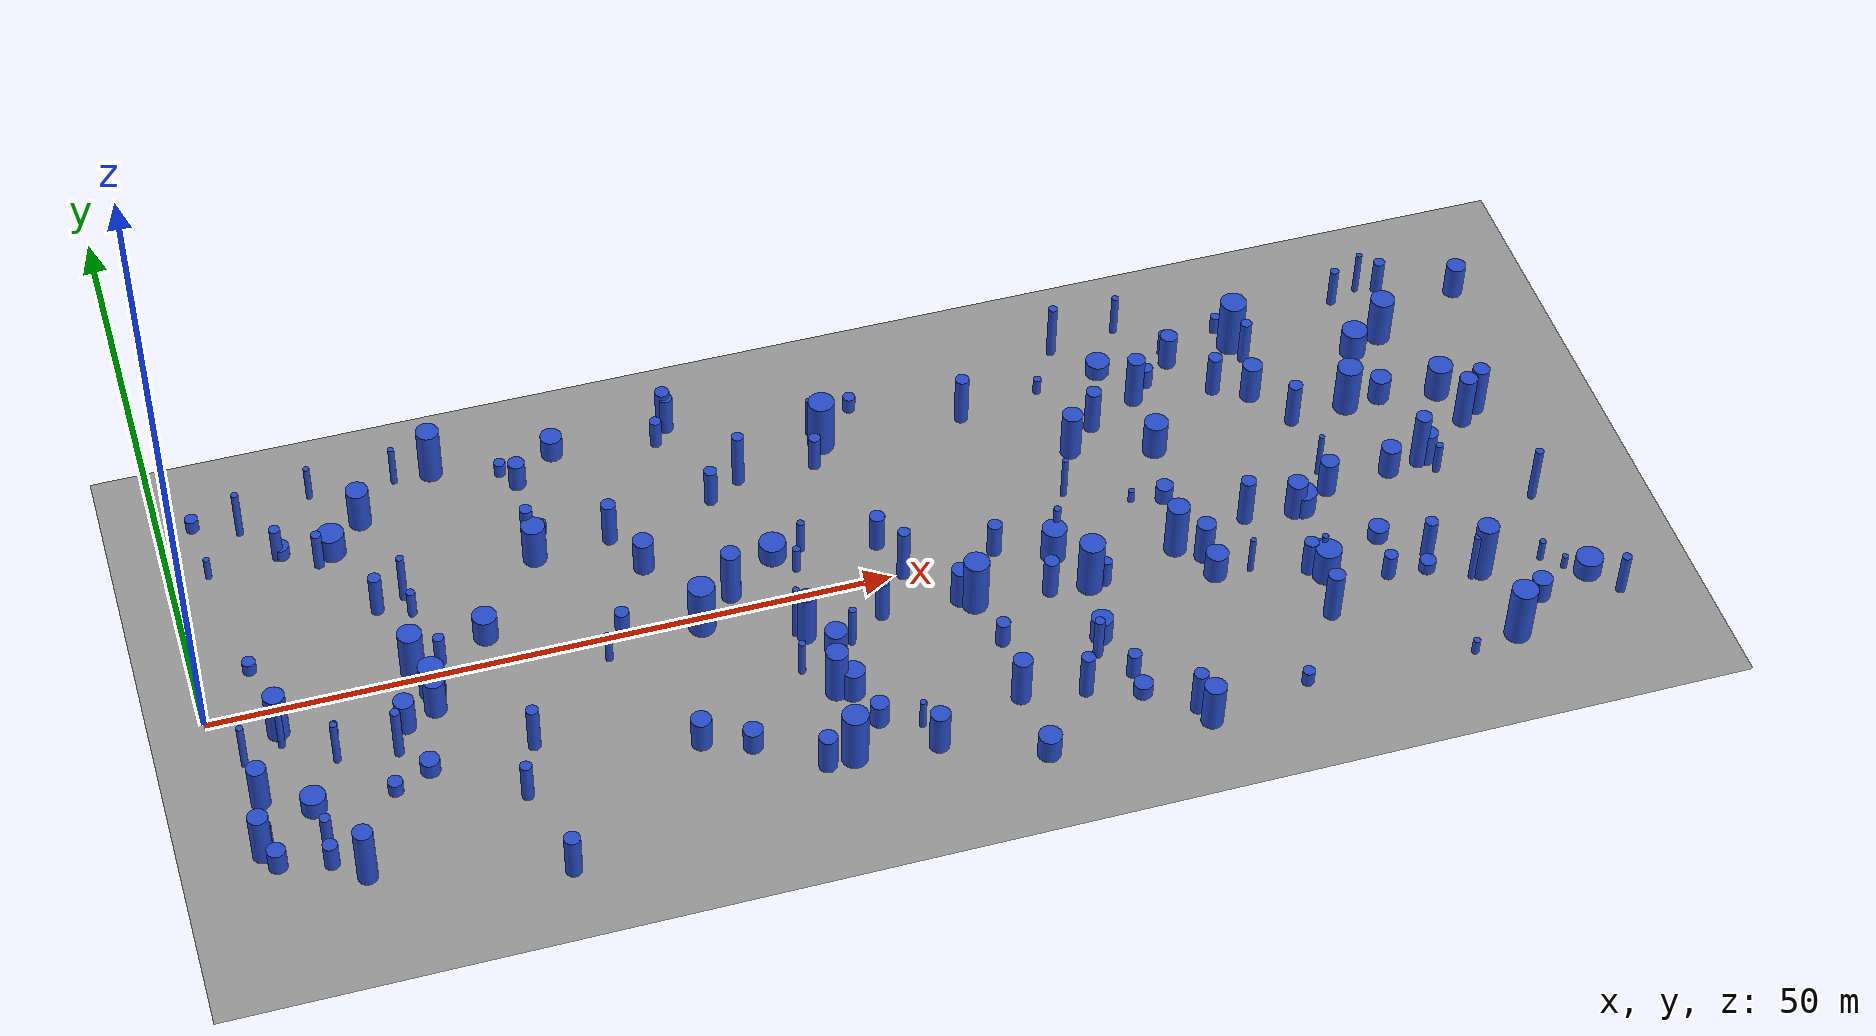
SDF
<sdf version="1.7">
 <world name="default">
  <light name="sun" type="directional">
   <pose>0 0 10 0 -0 0</pose>
   <diffuse>0.8 0.8 0.8 1</diffuse>
   <specular>0.2 0.2 0.2 1</specular>
   <attenuation>
    <range>1000</range>
    <constant>0.9</constant>
    <linear>0.01</linear>
    <quadratic>0.001</quadratic>
   </attenuation>
   <direction>-0.5 0.1 -0.9</direction>
   <spot><inner_angle>0</inner_angle><outer_angle>0</outer_angle><falloff>0</falloff></spot>
  </light>
  <gravity>0 0 -9.8</gravity>
  <magnetic_field>6e-06 2.3e-05 -4.2e-05</magnetic_field>
  <atmosphere type="adiabatic"/>
  <physics type="ode">
   <max_step_size>0.001</max_step_size>
   <real_time_factor>1</real_time_factor>
   <real_time_update_rate>1000</real_time_update_rate>
  </physics>
  <scene><ambient>0.4 0.4 0.4 1</ambient><background>0.7 0.7 0.7 1</background><shadows>1</shadows></scene>
  <audio><device>default</device></audio>
  <spherical_coordinates>
   <surface_model>EARTH_WGS84</surface_model>
   <latitude_deg>0</latitude_deg>
   <longitude_deg>0</longitude_deg>
   <elevation>0</elevation>
   <heading_deg>0</heading_deg>
  </spherical_coordinates>
  <model name="ground_plane_map">
   <static>1</static>
   <link name="link">
    <collision name="collision">
     <geometry><plane><normal>0 0 1</normal><size>110 50</size></plane></geometry>
     <surface>
      <contact><collide_bitmask>65535</collide_bitmask></contact>
      <friction><ode><mu>10000</mu><mu2>10000</mu2></ode></friction>
     </surface>
     <max_contacts>100</max_contacts>
    </collision>
    <visual name="visual">
     <cast_shadows>0</cast_shadows>
     <geometry><plane><normal>0 0 1</normal><size>110 50</size></plane></geometry>
     <material>
      <script><uri>file://media/materials/scripts/gazebo.material</uri><name>Gazebo/Grey</name></script>
     </material>
    </visual>
   </link>
   <pose>51 0 0 0 -0 0</pose>
  </model>
  <model name="0">
   <static>1</static>
   <link name="link">
    <inertial>
     <mass>2</mass>
     <inertia><ixx>3.51914</ixx><ixy>0</ixy><ixz>0</ixz><iyy>3.51914</iyy><iyz>0</iyz><izz>0.650222</izz></inertia>
    </inertial>
    <collision name="collision">
     <geometry><cylinder><length>4.37769</length><radius>0.806364</radius></cylinder></geometry>
     <surface><contact><collide_without_contact>0</collide_without_contact></contact></surface>
    </collision>
    <visual name="visual">
     <geometry><cylinder><length>4.37769</length><radius>0.806364</radius></cylinder></geometry>
     <material>
      <script><uri>file://media/materials/scripts/gazebo.material</uri><name>Gazebo/Blue</name></script>
     </material>
    </visual>
    <gravity>0</gravity>
   </link>
   <pose>43.1853 -9.25453 2.18884 0 -0 0</pose>
  </model>
  <model name="1">
   <static>1</static>
   <link name="link">
    <inertial>
     <mass>2</mass>
     <inertia><ixx>1.6827</ixx><ixy>0</ixy><ixz>0</ixz><iyy>1.6827</iyy><iyz>0</iyz><izz>0.274521</izz></inertia>
    </inertial>
    <collision name="collision">
     <geometry><cylinder><length>3.0451</length><radius>0.523947</radius></cylinder></geometry>
     <surface><contact><collide_without_contact>0</collide_without_contact></contact></surface>
    </collision>
    <visual name="visual">
     <geometry><cylinder><length>3.0451</length><radius>0.523947</radius></cylinder></geometry>
     <material>
      <script><uri>file://media/materials/scripts/gazebo.material</uri><name>Gazebo/Blue</name></script>
     </material>
    </visual>
    <gravity>0</gravity>
   </link>
   <pose>79.0825 -7.66138 1.52255 0 -0 0</pose>
  </model>
  <model name="2">
   <static>1</static>
   <link name="link">
    <inertial>
     <mass>2</mass>
     <inertia><ixx>1.6301</ixx><ixy>0</ixy><ixz>0</ixz><iyy>1.6301</iyy><iyz>0</iyz><izz>0.444496</izz></inertia>
    </inertial>
    <collision name="collision">
     <geometry><cylinder><length>2.90639</length><radius>0.666706</radius></cylinder></geometry>
     <surface><contact><collide_without_contact>0</collide_without_contact></contact></surface>
    </collision>
    <visual name="visual">
     <geometry><cylinder><length>2.90639</length><radius>0.666706</radius></cylinder></geometry>
     <material>
      <script><uri>file://media/materials/scripts/gazebo.material</uri><name>Gazebo/Blue</name></script>
     </material>
    </visual>
    <gravity>0</gravity>
   </link>
   <pose>91.2671 0.181225 1.45319 0 -0 0</pose>
  </model>
  <model name="3">
   <static>1</static>
   <link name="link">
    <inertial>
     <mass>2</mass>
     <inertia><ixx>1.078</ixx><ixy>0</ixy><ixz>0</ixz><iyy>1.078</iyy><iyz>0</iyz><izz>0.647451</izz></inertia>
    </inertial>
    <collision name="collision">
     <geometry><cylinder><length>2.12735</length><radius>0.804643</radius></cylinder></geometry>
     <surface><contact><collide_without_contact>0</collide_without_contact></contact></surface>
    </collision>
    <visual name="visual">
     <geometry><cylinder><length>2.12735</length><radius>0.804643</radius></cylinder></geometry>
     <material>
      <script><uri>file://media/materials/scripts/gazebo.material</uri><name>Gazebo/Blue</name></script>
     </material>
    </visual>
    <gravity>0</gravity>
   </link>
   <pose>62.6464 -9.57824 1.06368 0 -0 0</pose>
  </model>
  <model name="4">
   <static>1</static>
   <link name="link">
    <inertial>
     <mass>2</mass>
     <inertia><ixx>4.07302</ixx><ixy>0</ixy><ixz>0</ixz><iyy>4.07302</iyy><iyz>0</iyz><izz>0.972646</izz></inertia>
    </inertial>
    <collision name="collision">
     <geometry><cylinder><length>4.63899</length><radius>0.986228</radius></cylinder></geometry>
     <surface><contact><collide_without_contact>0</collide_without_contact></contact></surface>
    </collision>
    <visual name="visual">
     <geometry><cylinder><length>4.63899</length><radius>0.986228</radius></cylinder></geometry>
     <material>
      <script><uri>file://media/materials/scripts/gazebo.material</uri><name>Gazebo/Blue</name></script>
     </material>
    </visual>
    <gravity>0</gravity>
   </link>
   <pose>81.4098 15.2934 2.31949 0 -0 0</pose>
  </model>
  <model name="5">
   <static>1</static>
   <link name="link">
    <inertial>
     <mass>2</mass>
     <inertia><ixx>1.14393</ixx><ixy>0</ixy><ixz>0</ixz><iyy>1.14393</iyy><iyz>0</iyz><izz>0.614445</izz></inertia>
    </inertial>
    <collision name="collision">
     <geometry><cylinder><length>2.24059</length><radius>0.783865</radius></cylinder></geometry>
     <surface><contact><collide_without_contact>0</collide_without_contact></contact></surface>
    </collision>
    <visual name="visual">
     <geometry><cylinder><length>2.24059</length><radius>0.783865</radius></cylinder></geometry>
     <material>
      <script><uri>file://media/materials/scripts/gazebo.material</uri><name>Gazebo/Blue</name></script>
     </material>
    </visual>
    <gravity>0</gravity>
   </link>
   <pose>90.2586 7.07092 1.1203 0 -0 0</pose>
  </model>
  <model name="6">
   <static>1</static>
   <link name="link">
    <inertial>
     <mass>2</mass>
     <inertia><ixx>1.43</ixx><ixy>0</ixy><ixz>0</ixz><iyy>1.43</iyy><iyz>0</iyz><izz>0.0787145</izz></inertia>
    </inertial>
    <collision name="collision">
     <geometry><cylinder><length>2.88857</length><radius>0.280561</radius></cylinder></geometry>
     <surface><contact><collide_without_contact>0</collide_without_contact></contact></surface>
    </collision>
    <visual name="visual">
     <geometry><cylinder><length>2.88857</length><radius>0.280561</radius></cylinder></geometry>
     <material>
      <script><uri>file://media/materials/scripts/gazebo.material</uri><name>Gazebo/Blue</name></script>
     </material>
    </visual>
    <gravity>0</gravity>
   </link>
   <pose>44.4541 4.37326 1.44429 0 -0 0</pose>
  </model>
  <model name="7">
   <static>1</static>
   <link name="link">
    <inertial>
     <mass>2</mass>
     <inertia><ixx>4.08056</ixx><ixy>0</ixy><ixz>0</ixz><iyy>4.08056</iyy><iyz>0</iyz><izz>0.947284</izz></inertia>
    </inertial>
    <collision name="collision">
     <geometry><cylinder><length>4.65204</length><radius>0.973285</radius></cylinder></geometry>
     <surface><contact><collide_without_contact>0</collide_without_contact></contact></surface>
    </collision>
    <visual name="visual">
     <geometry><cylinder><length>4.65204</length><radius>0.973285</radius></cylinder></geometry>
     <material>
      <script><uri>file://media/materials/scripts/gazebo.material</uri><name>Gazebo/Blue</name></script>
     </material>
    </visual>
    <gravity>0</gravity>
   </link>
   <pose>48.7457 13.9013 2.32602 0 -0 0</pose>
  </model>
  <model name="8">
   <static>1</static>
   <link name="link">
    <inertial>
     <mass>2</mass>
     <inertia><ixx>1.05113</ixx><ixy>0</ixy><ixz>0</ixz><iyy>1.05113</iyy><iyz>0</iyz><izz>0.712374</izz></inertia>
    </inertial>
    <collision name="collision">
     <geometry><cylinder><length>2.04197</length><radius>0.844022</radius></cylinder></geometry>
     <surface><contact><collide_without_contact>0</collide_without_contact></contact></surface>
    </collision>
    <visual name="visual">
     <geometry><cylinder><length>2.04197</length><radius>0.844022</radius></cylinder></geometry>
     <material>
      <script><uri>file://media/materials/scripts/gazebo.material</uri><name>Gazebo/Blue</name></script>
     </material>
    </visual>
    <gravity>0</gravity>
   </link>
   <pose>55.7877 -18.618 1.02099 0 -0 0</pose>
  </model>
  <model name="9">
   <static>1</static>
   <link name="link">
    <inertial>
     <mass>2</mass>
     <inertia><ixx>2.64225</ixx><ixy>0</ixy><ixz>0</ixz><iyy>2.64225</iyy><iyz>0</iyz><izz>0.269422</izz></inertia>
    </inertial>
    <collision name="collision">
     <geometry><cylinder><length>3.87882</length><radius>0.519059</radius></cylinder></geometry>
     <surface><contact><collide_without_contact>0</collide_without_contact></contact></surface>
    </collision>
    <visual name="visual">
     <geometry><cylinder><length>3.87882</length><radius>0.519059</radius></cylinder></geometry>
     <material>
      <script><uri>file://media/materials/scripts/gazebo.material</uri><name>Gazebo/Blue</name></script>
     </material>
    </visual>
    <gravity>0</gravity>
   </link>
   <pose>83.1473 6.55157 1.93941 0 -0 0</pose>
  </model>
  <model name="10">
   <static>1</static>
   <link name="link">
    <inertial>
     <mass>2</mass>
     <inertia>
      <ixx>0.345124</ixx>
      <ixy>0</ixy>
      <ixz>0</ixz>
      <iyy>0.345124</iyy>
      <iyz>0</iyz>
      <izz>0.353861</izz>
     </inertia>
    </inertial>
    <collision name="collision">
     <geometry><cylinder><length>1.00457</length><radius>0.594862</radius></cylinder></geometry>
     <surface><contact><collide_without_contact>0</collide_without_contact></contact></surface>
    </collision>
    <visual name="visual">
     <geometry><cylinder><length>1.00457</length><radius>0.594862</radius></cylinder></geometry>
     <material>
      <script><uri>file://media/materials/scripts/gazebo.material</uri><name>Gazebo/Blue</name></script>
     </material>
    </visual>
    <gravity>0</gravity>
   </link>
   <pose>87.3229 -9.93889 0.502286 0 -0 0</pose>
  </model>
  <model name="11">
   <static>1</static>
   <link name="link">
    <inertial>
     <mass>2</mass>
     <inertia><ixx>1.28404</ixx><ixy>0</ixy><ixz>0</ixz><iyy>1.28404</iyy><iyz>0</iyz><izz>0.803492</izz></inertia>
    </inertial>
    <collision name="collision">
     <geometry><cylinder><length>2.30082</length><radius>0.896377</radius></cylinder></geometry>
     <surface><contact><collide_without_contact>0</collide_without_contact></contact></surface>
    </collision>
    <visual name="visual">
     <geometry><cylinder><length>2.30082</length><radius>0.896377</radius></cylinder></geometry>
     <material>
      <script><uri>file://media/materials/scripts/gazebo.material</uri><name>Gazebo/Blue</name></script>
     </material>
    </visual>
    <gravity>0</gravity>
   </link>
   <pose>20.6606 2.5794 1.15041 0 -0 0</pose>
  </model>
  <model name="12">
   <static>1</static>
   <link name="link">
    <inertial>
     <mass>2</mass>
     <inertia><ixx>1.11102</ixx><ixy>0</ixy><ixz>0</ixz><iyy>1.11102</iyy><iyz>0</iyz><izz>0.948739</izz></inertia>
    </inertial>
    <collision name="collision">
     <geometry><cylinder><length>1.95446</length><radius>0.974032</radius></cylinder></geometry>
     <surface><contact><collide_without_contact>0</collide_without_contact></contact></surface>
    </collision>
    <visual name="visual">
     <geometry><cylinder><length>1.95446</length><radius>0.974032</radius></cylinder></geometry>
     <material>
      <script><uri>file://media/materials/scripts/gazebo.material</uri><name>Gazebo/Blue</name></script>
     </material>
    </visual>
    <gravity>0</gravity>
   </link>
   <pose>80.7273 -1.97986 0.977232 0 -0 0</pose>
  </model>
  <model name="13">
   <static>1</static>
   <link name="link">
    <inertial>
     <mass>2</mass>
     <inertia>
      <ixx>0.395173</ixx>
      <ixy>0</ixy>
      <ixz>0</ixz>
      <iyy>0.395173</iyy>
      <iyz>0</iyz>
      <izz>0.207976</izz>
     </inertia>
    </inertial>
    <collision name="collision">
     <geometry><cylinder><length>1.32178</length><radius>0.456044</radius></cylinder></geometry>
     <surface><contact><collide_without_contact>0</collide_without_contact></contact></surface>
    </collision>
    <visual name="visual">
     <geometry><cylinder><length>1.32178</length><radius>0.456044</radius></cylinder></geometry>
     <material>
      <script><uri>file://media/materials/scripts/gazebo.material</uri><name>Gazebo/Blue</name></script>
     </material>
    </visual>
    <gravity>0</gravity>
   </link>
   <pose>51.7868 16.9186 0.660892 0 -0 0</pose>
  </model>
  <model name="14">
   <static>1</static>
   <link name="link">
    <inertial>
     <mass>2</mass>
     <inertia>
      <ixx>0.549243</ixx>
      <ixy>0</ixy>
      <ixz>0</ixz>
      <iyy>0.549243</iyy>
      <iyz>0</iyz>
      <izz>0.410899</izz>
     </inertia>
    </inertial>
    <collision name="collision">
     <geometry><cylinder><length>1.43623</length><radius>0.641014</radius></cylinder></geometry>
     <surface><contact><collide_without_contact>0</collide_without_contact></contact></surface>
    </collision>
    <visual name="visual">
     <geometry><cylinder><length>1.43623</length><radius>0.641014</radius></cylinder></geometry>
     <material>
      <script><uri>file://media/materials/scripts/gazebo.material</uri><name>Gazebo/Blue</name></script>
     </material>
    </visual>
    <gravity>0</gravity>
   </link>
   <pose>71.3913 1.83682 0.718116 0 -0 0</pose>
  </model>
  <model name="15">
   <static>1</static>
   <link name="link">
    <inertial>
     <mass>2</mass>
     <inertia><ixx>3.22143</ixx><ixy>0</ixy><ixz>0</ixz><iyy>3.22143</iyy><iyz>0</iyz><izz>0.399711</izz></inertia>
    </inertial>
    <collision name="collision">
     <geometry><cylinder><length>4.25787</length><radius>0.632227</radius></cylinder></geometry>
     <surface><contact><collide_without_contact>0</collide_without_contact></contact></surface>
    </collision>
    <visual name="visual">
     <geometry><cylinder><length>4.25787</length><radius>0.632227</radius></cylinder></geometry>
     <material>
      <script><uri>file://media/materials/scripts/gazebo.material</uri><name>Gazebo/Blue</name></script>
     </material>
    </visual>
    <gravity>0</gravity>
   </link>
   <pose>96.7974 3.99695 2.12893 0 -0 0</pose>
  </model>
  <model name="16">
   <static>1</static>
   <link name="link">
    <inertial>
     <mass>2</mass>
     <inertia><ixx>2.0255</ixx><ixy>0</ixy><ixz>0</ixz><iyy>2.0255</iyy><iyz>0</iyz><izz>0.309126</izz></inertia>
    </inertial>
    <collision name="collision">
     <geometry><cylinder><length>3.35047</length><radius>0.555991</radius></cylinder></geometry>
     <surface><contact><collide_without_contact>0</collide_without_contact></contact></surface>
    </collision>
    <visual name="visual">
     <geometry><cylinder><length>3.35047</length><radius>0.555991</radius></cylinder></geometry>
     <material>
      <script><uri>file://media/materials/scripts/gazebo.material</uri><name>Gazebo/Blue</name></script>
     </material>
    </visual>
    <gravity>0</gravity>
   </link>
   <pose>60.5216 -4.47597 1.67523 0 -0 0</pose>
  </model>
  <model name="17">
   <static>1</static>
   <link name="link">
    <inertial>
     <mass>2</mass>
     <inertia><ixx>1.91129</ixx><ixy>0</ixy><ixz>0</ixz><iyy>1.91129</iyy><iyz>0</iyz><izz>0.186852</izz></inertia>
    </inertial>
    <collision name="collision">
     <geometry><cylinder><length>3.3026</length><radius>0.432264</radius></cylinder></geometry>
     <surface><contact><collide_without_contact>0</collide_without_contact></contact></surface>
    </collision>
    <visual name="visual">
     <geometry><cylinder><length>3.3026</length><radius>0.432264</radius></cylinder></geometry>
     <material>
      <script><uri>file://media/materials/scripts/gazebo.material</uri><name>Gazebo/Blue</name></script>
     </material>
    </visual>
    <gravity>0</gravity>
   </link>
   <pose>20.2077 -12.26 1.6513 0 -0 0</pose>
  </model>
  <model name="18">
   <static>1</static>
   <link name="link">
    <inertial>
     <mass>2</mass>
     <inertia><ixx>2.24806</ixx><ixy>0</ixy><ixz>0</ixz><iyy>2.24806</iyy><iyz>0</iyz><izz>0.5261</izz></inertia>
    </inertial>
    <collision name="collision">
     <geometry><cylinder><length>3.45109</length><radius>0.725328</radius></cylinder></geometry>
     <surface><contact><collide_without_contact>0</collide_without_contact></contact></surface>
    </collision>
    <visual name="visual">
     <geometry><cylinder><length>3.45109</length><radius>0.725328</radius></cylinder></geometry>
     <material>
      <script><uri>file://media/materials/scripts/gazebo.material</uri><name>Gazebo/Blue</name></script>
     </material>
    </visual>
    <gravity>0</gravity>
   </link>
   <pose>48.6871 -15.812 1.72555 0 -0 0</pose>
  </model>
  <model name="19">
   <static>1</static>
   <link name="link">
    <inertial>
     <mass>2</mass>
     <inertia><ixx>3.11365</ixx><ixy>0</ixy><ixz>0</ixz><iyy>3.11365</iyy><iyz>0</iyz><izz>0.812551</izz></inertia>
    </inertial>
    <collision name="collision">
     <geometry><cylinder><length>4.03042</length><radius>0.901416</radius></cylinder></geometry>
     <surface><contact><collide_without_contact>0</collide_without_contact></contact></surface>
    </collision>
    <visual name="visual">
     <geometry><cylinder><length>4.03042</length><radius>0.901416</radius></cylinder></geometry>
     <material>
      <script><uri>file://media/materials/scripts/gazebo.material</uri><name>Gazebo/Blue</name></script>
     </material>
    </visual>
    <gravity>0</gravity>
   </link>
   <pose>92.5748 13.081 2.01521 0 -0 0</pose>
  </model>
  <model name="20">
   <static>1</static>
   <link name="link">
    <inertial>
     <mass>2</mass>
     <inertia><ixx>3.95583</ixx><ixy>0</ixy><ixz>0</ixz><iyy>3.95583</iyy><iyz>0</iyz><izz>0.880718</izz></inertia>
    </inertial>
    <collision name="collision">
     <geometry><cylinder><length>4.59269</length><radius>0.938466</radius></cylinder></geometry>
     <surface><contact><collide_without_contact>0</collide_without_contact></contact></surface>
    </collision>
    <visual name="visual">
     <geometry><cylinder><length>4.59269</length><radius>0.938466</radius></cylinder></geometry>
     <material>
      <script><uri>file://media/materials/scripts/gazebo.material</uri><name>Gazebo/Blue</name></script>
     </material>
    </visual>
    <gravity>0</gravity>
   </link>
   <pose>54.9838 -4.14413 2.29635 0 -0 0</pose>
  </model>
  <model name="21">
   <static>1</static>
   <link name="link">
    <inertial>
     <mass>2</mass>
     <inertia><ixx>2.52192</ixx><ixy>0</ixy><ixz>0</ixz><iyy>2.52192</iyy><iyz>0</iyz><izz>0.176826</izz></inertia>
    </inertial>
    <collision name="collision">
     <geometry><cylinder><length>3.82113</length><radius>0.420507</radius></cylinder></geometry>
     <surface><contact><collide_without_contact>0</collide_without_contact></contact></surface>
    </collision>
    <visual name="visual">
     <geometry><cylinder><length>3.82113</length><radius>0.420507</radius></cylinder></geometry>
     <material>
      <script><uri>file://media/materials/scripts/gazebo.material</uri><name>Gazebo/Blue</name></script>
     </material>
    </visual>
    <gravity>0</gravity>
   </link>
   <pose>81.9008 13.6855 1.91057 0 -0 0</pose>
  </model>
  <model name="22">
   <static>1</static>
   <link name="link">
    <inertial>
     <mass>2</mass>
     <inertia><ixx>3.72199</ixx><ixy>0</ixy><ixz>0</ixz><iyy>3.72199</iyy><iyz>0</iyz><izz>0.45137</izz></inertia>
    </inertial>
    <collision name="collision">
     <geometry><cylinder><length>4.58016</length><radius>0.671841</radius></cylinder></geometry>
     <surface><contact><collide_without_contact>0</collide_without_contact></contact></surface>
    </collision>
    <visual name="visual">
     <geometry><cylinder><length>4.58016</length><radius>0.671841</radius></cylinder></geometry>
     <material>
      <script><uri>file://media/materials/scripts/gazebo.material</uri><name>Gazebo/Blue</name></script>
     </material>
    </visual>
    <gravity>0</gravity>
   </link>
   <pose>95.3721 3.08072 2.29008 0 -0 0</pose>
  </model>
  <model name="23">
   <static>1</static>
   <link name="link">
    <inertial>
     <mass>2</mass>
     <inertia><ixx>1.5739</ixx><ixy>0</ixy><ixz>0</ixz><iyy>1.5739</iyy><iyz>0</iyz><izz>0.53027</izz></inertia>
    </inertial>
    <collision name="collision">
     <geometry><cylinder><length>2.80225</length><radius>0.728196</radius></cylinder></geometry>
     <surface><contact><collide_without_contact>0</collide_without_contact></contact></surface>
    </collision>
    <visual name="visual">
     <geometry><cylinder><length>2.80225</length><radius>0.728196</radius></cylinder></geometry>
     <material>
      <script><uri>file://media/materials/scripts/gazebo.material</uri><name>Gazebo/Blue</name></script>
     </material>
    </visual>
    <gravity>0</gravity>
   </link>
   <pose>99.903 16.0704 1.40113 0 -0 0</pose>
  </model>
  <model name="24">
   <static>1</static>
   <link name="link">
    <inertial>
     <mass>2</mass>
     <inertia><ixx>2.93809</ixx><ixy>0</ixy><ixz>0</ixz><iyy>2.93809</iyy><iyz>0</iyz><izz>0.070702</izz></inertia>
    </inertial>
    <collision name="collision">
     <geometry><cylinder><length>4.1733</length><radius>0.265898</radius></cylinder></geometry>
     <surface><contact><collide_without_contact>0</collide_without_contact></contact></surface>
    </collision>
    <visual name="visual">
     <geometry><cylinder><length>4.1733</length><radius>0.265898</radius></cylinder></geometry>
     <material>
      <script><uri>file://media/materials/scripts/gazebo.material</uri><name>Gazebo/Blue</name></script>
     </material>
    </visual>
    <gravity>0</gravity>
   </link>
   <pose>62.2183 -0.535023 2.08665 0 -0 0</pose>
  </model>
  <model name="25">
   <static>1</static>
   <link name="link">
    <inertial>
     <mass>2</mass>
     <inertia><ixx>2.4495</ixx><ixy>0</ixy><ixz>0</ixz><iyy>2.4495</iyy><iyz>0</iyz><izz>0.767485</izz></inertia>
    </inertial>
    <collision name="collision">
     <geometry><cylinder><length>3.52059</length><radius>0.876062</radius></cylinder></geometry>
     <surface><contact><collide_without_contact>0</collide_without_contact></contact></surface>
    </collision>
    <visual name="visual">
     <geometry><cylinder><length>3.52059</length><radius>0.876062</radius></cylinder></geometry>
     <material>
      <script><uri>file://media/materials/scripts/gazebo.material</uri><name>Gazebo/Blue</name></script>
     </material>
    </visual>
    <gravity>0</gravity>
   </link>
   <pose>25.7538 8.85397 1.76029 0 -0 0</pose>
  </model>
  <model name="26">
   <static>1</static>
   <link name="link">
    <inertial>
     <mass>2</mass>
     <inertia><ixx>0.43026</ixx><ixy>0</ixy><ixz>0</ixz><iyy>0.43026</iyy><iyz>0</iyz><izz>0.141653</izz></inertia>
    </inertial>
    <collision name="collision">
     <geometry><cylinder><length>1.46854</length><radius>0.376368</radius></cylinder></geometry>
     <surface><contact><collide_without_contact>0</collide_without_contact></contact></surface>
    </collision>
    <visual name="visual">
     <geometry><cylinder><length>1.46854</length><radius>0.376368</radius></cylinder></geometry>
     <material>
      <script><uri>file://media/materials/scripts/gazebo.material</uri><name>Gazebo/Blue</name></script>
     </material>
    </visual>
    <gravity>0</gravity>
   </link>
   <pose>80.2366 -6.5725 0.734269 0 -0 0</pose>
  </model>
  <model name="27">
   <static>1</static>
   <link name="link">
    <inertial>
     <mass>2</mass>
     <inertia>
      <ixx>3.06912</ixx>
      <ixy>0</ixy>
      <ixz>0</ixz>
      <iyy>3.06912</iyy>
      <iyz>0</iyz>
      <izz>0.0786724</izz>
     </inertia>
    </inertial>
    <collision name="collision">
     <geometry><cylinder><length>4.26365</length><radius>0.280486</radius></cylinder></geometry>
     <surface><contact><collide_without_contact>0</collide_without_contact></contact></surface>
    </collision>
    <visual name="visual">
     <geometry><cylinder><length>4.26365</length><radius>0.280486</radius></cylinder></geometry>
     <material>
      <script><uri>file://media/materials/scripts/gazebo.material</uri><name>Gazebo/Blue</name></script>
     </material>
    </visual>
    <gravity>0</gravity>
   </link>
   <pose>15.8342 7.79594 2.13183 0 -0 0</pose>
  </model>
  <model name="28">
   <static>1</static>
   <link name="link">
    <inertial>
     <mass>2</mass>
     <inertia>
      <ixx>0.449637</ixx>
      <ixy>0</ixy>
      <ixz>0</ixz>
      <iyy>0.449637</iyy>
      <iyz>0</iyz>
      <izz>0.434403</izz>
     </inertia>
    </inertial>
    <collision name="collision">
     <geometry><cylinder><length>1.18094</length><radius>0.659093</radius></cylinder></geometry>
     <surface><contact><collide_without_contact>0</collide_without_contact></contact></surface>
    </collision>
    <visual name="visual">
     <geometry><cylinder><length>1.18094</length><radius>0.659093</radius></cylinder></geometry>
     <material>
      <script><uri>file://media/materials/scripts/gazebo.material</uri><name>Gazebo/Blue</name></script>
     </material>
    </visual>
    <gravity>0</gravity>
   </link>
   <pose>91.4611 1.32284 0.590468 0 -0 0</pose>
  </model>
  <model name="29">
   <static>1</static>
   <link name="link">
    <inertial>
     <mass>2</mass>
     <inertia>
      <ixx>2.33382</ixx>
      <ixy>0</ixy>
      <ixz>0</ixz>
      <iyy>2.33382</iyy>
      <iyz>0</iyz>
      <izz>0.0489991</izz>
     </inertia>
    </inertial>
    <collision name="collision">
     <geometry><cylinder><length>3.72236</length><radius>0.221357</radius></cylinder></geometry>
     <surface><contact><collide_without_contact>0</collide_without_contact></contact></surface>
    </collision>
    <visual name="visual">
     <geometry><cylinder><length>3.72236</length><radius>0.221357</radius></cylinder></geometry>
     <material>
      <script><uri>file://media/materials/scripts/gazebo.material</uri><name>Gazebo/Blue</name></script>
     </material>
    </visual>
    <gravity>0</gravity>
   </link>
   <pose>64.4402 4.20646 1.86118 0 -0 0</pose>
  </model>
  <model name="30">
   <static>1</static>
   <link name="link">
    <inertial>
     <mass>2</mass>
     <inertia><ixx>1.95076</ixx><ixy>0</ixy><ixz>0</ixz><iyy>1.95076</iyy><iyz>0</iyz><izz>0.263136</izz></inertia>
    </inertial>
    <collision name="collision">
     <geometry><cylinder><length>3.30381</length><radius>0.512968</radius></cylinder></geometry>
     <surface><contact><collide_without_contact>0</collide_without_contact></contact></surface>
    </collision>
    <visual name="visual">
     <geometry><cylinder><length>3.30381</length><radius>0.512968</radius></cylinder></geometry>
     <material>
      <script><uri>file://media/materials/scripts/gazebo.material</uri><name>Gazebo/Blue</name></script>
     </material>
    </visual>
    <gravity>0</gravity>
   </link>
   <pose>38.1472 18.7277 1.65191 0 -0 0</pose>
  </model>
  <model name="31">
   <static>1</static>
   <link name="link">
    <inertial>
     <mass>2</mass>
     <inertia>
      <ixx>0.242333</ixx>
      <ixy>0</ixy>
      <ixz>0</ixz>
      <iyy>0.242333</iyy>
      <iyz>0</iyz>
      <izz>0.0472233</izz>
     </inertia>
    </inertial>
    <collision name="collision">
     <geometry><cylinder><length>1.14557</length><radius>0.217309</radius></cylinder></geometry>
     <surface><contact><collide_without_contact>0</collide_without_contact></contact></surface>
    </collision>
    <visual name="visual">
     <geometry><cylinder><length>1.14557</length><radius>0.217309</radius></cylinder></geometry>
     <material>
      <script><uri>file://media/materials/scripts/gazebo.material</uri><name>Gazebo/Blue</name></script>
     </material>
    </visual>
    <gravity>0</gravity>
   </link>
   <pose>96.9028 -12.4642 0.572784 0 -0 0</pose>
  </model>
  <model name="32">
   <static>1</static>
   <link name="link">
    <inertial>
     <mass>2</mass>
     <inertia>
      <ixx>0.440675</ixx>
      <ixy>0</ixy>
      <ixz>0</ixz>
      <iyy>0.440675</iyy>
      <iyz>0</iyz>
      <izz>0.135764</izz>
     </inertia>
    </inertial>
    <collision name="collision">
     <geometry><cylinder><length>1.49558</length><radius>0.368461</radius></cylinder></geometry>
     <surface><contact><collide_without_contact>0</collide_without_contact></contact></surface>
    </collision>
    <visual name="visual">
     <geometry><cylinder><length>1.49558</length><radius>0.368461</radius></cylinder></geometry>
     <material>
      <script><uri>file://media/materials/scripts/gazebo.material</uri><name>Gazebo/Blue</name></script>
     </material>
    </visual>
    <gravity>0</gravity>
   </link>
   <pose>80.853 17.1568 0.74779 0 -0 0</pose>
  </model>
  <model name="33">
   <static>1</static>
   <link name="link">
    <inertial>
     <mass>2</mass>
     <inertia>
      <ixx>0.344495</ixx>
      <ixy>0</ixy>
      <ixz>0</ixz>
      <iyy>0.344495</iyy>
      <iyz>0</iyz>
      <izz>0.292135</izz>
     </inertia>
    </inertial>
    <collision name="collision">
     <geometry><cylinder><length>1.09113</length><radius>0.540495</radius></cylinder></geometry>
     <surface><contact><collide_without_contact>0</collide_without_contact></contact></surface>
    </collision>
    <visual name="visual">
     <geometry><cylinder><length>1.09113</length><radius>0.540495</radius></cylinder></geometry>
     <material>
      <script><uri>file://media/materials/scripts/gazebo.material</uri><name>Gazebo/Blue</name></script>
     </material>
    </visual>
    <gravity>0</gravity>
   </link>
   <pose>11.5808 -9.34368 0.545565 0 -0 0</pose>
  </model>
  <model name="34">
   <static>1</static>
   <link name="link">
    <inertial>
     <mass>2</mass>
     <inertia>
      <ixx>0.848579</ixx>
      <ixy>0</ixy>
      <ixz>0</ixz>
      <iyy>0.848579</iyy>
      <iyz>0</iyz>
      <izz>0.514864</izz>
     </inertia>
    </inertial>
    <collision name="collision">
     <geometry><cylinder><length>1.88332</length><radius>0.717541</radius></cylinder></geometry>
     <surface><contact><collide_without_contact>0</collide_without_contact></contact></surface>
    </collision>
    <visual name="visual">
     <geometry><cylinder><length>1.88332</length><radius>0.717541</radius></cylinder></geometry>
     <material>
      <script><uri>file://media/materials/scripts/gazebo.material</uri><name>Gazebo/Blue</name></script>
     </material>
    </visual>
    <gravity>0</gravity>
   </link>
   <pose>36.2442 -12.3285 0.941659 0 -0 0</pose>
  </model>
  <model name="35">
   <static>1</static>
   <link name="link">
    <inertial>
     <mass>2</mass>
     <inertia>
      <ixx>1.54138</ixx>
      <ixy>0</ixy>
      <ixz>0</ixz>
      <iyy>1.54138</iyy>
      <iyz>0</iyz>
      <izz>0.0535936</izz>
     </inertia>
    </inertial>
    <collision name="collision">
     <geometry><cylinder><length>3.01455</length><radius>0.231503</radius></cylinder></geometry>
     <surface><contact><collide_without_contact>0</collide_without_contact></contact></surface>
    </collision>
    <visual name="visual">
     <geometry><cylinder><length>3.01455</length><radius>0.231503</radius></cylinder></geometry>
     <material>
      <script><uri>file://media/materials/scripts/gazebo.material</uri><name>Gazebo/Blue</name></script>
     </material>
    </visual>
    <gravity>0</gravity>
   </link>
   <pose>11.2769 19.3033 1.50727 0 -0 0</pose>
  </model>
  <model name="36">
   <static>1</static>
   <link name="link">
    <inertial>
     <mass>2</mass>
     <inertia>
      <ixx>0.656964</ixx>
      <ixy>0</ixy>
      <ixz>0</ixz>
      <iyy>0.656964</iyy>
      <iyz>0</iyz>
      <izz>0.237017</izz>
     </inertia>
    </inertial>
    <collision name="collision">
     <geometry><cylinder><length>1.79742</length><radius>0.486844</radius></cylinder></geometry>
     <surface><contact><collide_without_contact>0</collide_without_contact></contact></surface>
    </collision>
    <visual name="visual">
     <geometry><cylinder><length>1.79742</length><radius>0.486844</radius></cylinder></geometry>
     <material>
      <script><uri>file://media/materials/scripts/gazebo.material</uri><name>Gazebo/Blue</name></script>
     </material>
    </visual>
    <gravity>0</gravity>
   </link>
   <pose>73.9343 13.2036 0.898712 0 -0 0</pose>
  </model>
  <model name="37">
   <static>1</static>
   <link name="link">
    <inertial>
     <mass>2</mass>
     <inertia><ixx>3.69723</ixx><ixy>0</ixy><ixz>0</ixz><iyy>3.69723</iyy><iyz>0</iyz><izz>0.112587</izz></inertia>
    </inertial>
    <collision name="collision">
     <geometry><cylinder><length>4.67393</length><radius>0.33554</radius></cylinder></geometry>
     <surface><contact><collide_without_contact>0</collide_without_contact></contact></surface>
    </collision>
    <visual name="visual">
     <geometry><cylinder><length>4.67393</length><radius>0.33554</radius></cylinder></geometry>
     <material>
      <script><uri>file://media/materials/scripts/gazebo.material</uri><name>Gazebo/Blue</name></script>
     </material>
    </visual>
    <gravity>0</gravity>
   </link>
   <pose>68.1482 18.3489 2.33696 0 -0 0</pose>
  </model>
  <model name="38">
   <static>1</static>
   <link name="link">
    <inertial>
     <mass>2</mass>
     <inertia>
      <ixx>0.527566</ixx>
      <ixy>0</ixy>
      <ixz>0</ixz>
      <iyy>0.527566</iyy>
      <iyz>0</iyz>
      <izz>0.549024</izz>
     </inertia>
    </inertial>
    <collision name="collision">
     <geometry><cylinder><length>1.2322</length><radius>0.740961</radius></cylinder></geometry>
     <surface><contact><collide_without_contact>0</collide_without_contact></contact></surface>
    </collision>
    <visual name="visual">
     <geometry><cylinder><length>1.2322</length><radius>0.740961</radius></cylinder></geometry>
     <material>
      <script><uri>file://media/materials/scripts/gazebo.material</uri><name>Gazebo/Blue</name></script>
     </material>
    </visual>
    <gravity>0</gravity>
   </link>
   <pose>85.0306 -6.07382 0.616102 0 -0 0</pose>
  </model>
  <model name="39">
   <static>1</static>
   <link name="link">
    <inertial>
     <mass>2</mass>
     <inertia>
      <ixx>0.897959</ixx>
      <ixy>0</ixy>
      <ixz>0</ixz>
      <iyy>0.897959</iyy>
      <iyz>0</iyz>
      <izz>0.458916</izz>
     </inertia>
    </inertial>
    <collision name="collision">
     <geometry><cylinder><length>2.00275</length><radius>0.677433</radius></cylinder></geometry>
     <surface><contact><collide_without_contact>0</collide_without_contact></contact></surface>
    </collision>
    <visual name="visual">
     <geometry><cylinder><length>2.00275</length><radius>0.677433</radius></cylinder></geometry>
     <material>
      <script><uri>file://media/materials/scripts/gazebo.material</uri><name>Gazebo/Blue</name></script>
     </material>
    </visual>
    <gravity>0</gravity>
   </link>
   <pose>45.3096 -12.5666 1.00137 0 -0 0</pose>
  </model>
  <model name="40">
   <static>1</static>
   <link name="link">
    <inertial>
     <mass>2</mass>
     <inertia><ixx>1.528</ixx><ixy>0</ixy><ixz>0</ixz><iyy>1.528</iyy><iyz>0</iyz><izz>0.278704</izz></inertia>
    </inertial>
    <collision name="collision">
     <geometry><cylinder><length>2.8865</length><radius>0.527924</radius></cylinder></geometry>
     <surface><contact><collide_without_contact>0</collide_without_contact></contact></surface>
    </collision>
    <visual name="visual">
     <geometry><cylinder><length>2.8865</length><radius>0.527924</radius></cylinder></geometry>
     <material>
      <script><uri>file://media/materials/scripts/gazebo.material</uri><name>Gazebo/Blue</name></script>
     </material>
    </visual>
    <gravity>0</gravity>
   </link>
   <pose>57.8383 0.334925 1.44325 0 -0 0</pose>
  </model>
  <model name="41">
   <static>1</static>
   <link name="link">
    <inertial>
     <mass>2</mass>
     <inertia>
      <ixx>0.958554</ixx>
      <ixy>0</ixy>
      <ixz>0</ixz>
      <iyy>0.958554</iyy>
      <iyz>0</iyz>
      <izz>0.235925</izz>
     </inertia>
    </inertial>
    <collision name="collision">
     <geometry><cylinder><length>2.24578</length><radius>0.485721</radius></cylinder></geometry>
     <surface><contact><collide_without_contact>0</collide_without_contact></contact></surface>
    </collision>
    <visual name="visual">
     <geometry><cylinder><length>2.24578</length><radius>0.485721</radius></cylinder></geometry>
     <material>
      <script><uri>file://media/materials/scripts/gazebo.material</uri><name>Gazebo/Blue</name></script>
     </material>
    </visual>
    <gravity>0</gravity>
   </link>
   <pose>84.4381 -9.72074 1.12289 0 -0 0</pose>
  </model>
  <model name="42">
   <static>1</static>
   <link name="link">
    <inertial>
     <mass>2</mass>
     <inertia>
      <ixx>1.77423</ixx>
      <ixy>0</ixy>
      <ixz>0</ixz>
      <iyy>1.77423</iyy>
      <iyz>0</iyz>
      <izz>0.0440786</izz>
     </inertia>
    </inertial>
    <collision name="collision">
     <geometry><cylinder><length>3.2424</length><radius>0.209949</radius></cylinder></geometry>
     <surface><contact><collide_without_contact>0</collide_without_contact></contact></surface>
    </collision>
    <visual name="visual">
     <geometry><cylinder><length>3.2424</length><radius>0.209949</radius></cylinder></geometry>
     <material>
      <script><uri>file://media/materials/scripts/gazebo.material</uri><name>Gazebo/Blue</name></script>
     </material>
    </visual>
    <gravity>0</gravity>
   </link>
   <pose>75.056 -6.49444 1.6212 0 -0 0</pose>
  </model>
  <model name="43">
   <static>1</static>
   <link name="link">
    <inertial>
     <mass>2</mass>
     <inertia>
      <ixx>0.323352</ixx>
      <ixy>0</ixy>
      <ixz>0</ixz>
      <iyy>0.323352</iyy>
      <iyz>0</iyz>
      <izz>0.180376</izz>
     </inertia>
    </inertial>
    <collision name="collision">
     <geometry><cylinder><length>1.18279</length><radius>0.424707</radius></cylinder></geometry>
     <surface><contact><collide_without_contact>0</collide_without_contact></contact></surface>
    </collision>
    <visual name="visual">
     <geometry><cylinder><length>1.18279</length><radius>0.424707</radius></cylinder></geometry>
     <material>
      <script><uri>file://media/materials/scripts/gazebo.material</uri><name>Gazebo/Blue</name></script>
     </material>
    </visual>
    <gravity>0</gravity>
   </link>
   <pose>25.2338 17.7403 0.591393 0 -0 0</pose>
  </model>
  <model name="44">
   <static>1</static>
   <link name="link">
    <inertial>
     <mass>2</mass>
     <inertia><ixx>1.05972</ixx><ixy>0</ixy><ixz>0</ixz><iyy>1.05972</iyy><iyz>0</iyz><izz>0.18516</izz></inertia>
    </inertial>
    <collision name="collision">
     <geometry><cylinder><length>2.4089</length><radius>0.430302</radius></cylinder></geometry>
     <surface><contact><collide_without_contact>0</collide_without_contact></contact></surface>
    </collision>
    <visual name="visual">
     <geometry><cylinder><length>2.4089</length><radius>0.430302</radius></cylinder></geometry>
     <material>
      <script><uri>file://media/materials/scripts/gazebo.material</uri><name>Gazebo/Blue</name></script>
     </material>
    </visual>
    <gravity>0</gravity>
   </link>
   <pose>37.0413 17.4916 1.20445 0 -0 0</pose>
  </model>
  <model name="45">
   <static>1</static>
   <link name="link">
    <inertial>
     <mass>2</mass>
     <inertia><ixx>2.3255</ixx><ixy>0</ixy><ixz>0</ixz><iyy>2.3255</iyy><iyz>0</iyz><izz>0.485616</izz></inertia>
    </inertial>
    <collision name="collision">
     <geometry><cylinder><length>3.53499</length><radius>0.696861</radius></cylinder></geometry>
     <surface><contact><collide_without_contact>0</collide_without_contact></contact></surface>
    </collision>
    <visual name="visual">
     <geometry><cylinder><length>3.53499</length><radius>0.696861</radius></cylinder></geometry>
     <material>
      <script><uri>file://media/materials/scripts/gazebo.material</uri><name>Gazebo/Blue</name></script>
     </material>
    </visual>
    <gravity>0</gravity>
   </link>
   <pose>72.2614 -4.32324 1.7675 0 -0 0</pose>
  </model>
  <model name="46">
   <static>1</static>
   <link name="link">
    <inertial>
     <mass>2</mass>
     <inertia><ixx>1.43688</ixx><ixy>0</ixy><ixz>0</ixz><iyy>1.43688</iyy><iyz>0</iyz><izz>0.51936</izz></inertia>
    </inertial>
    <collision name="collision">
     <geometry><cylinder><length>2.65767</length><radius>0.720666</radius></cylinder></geometry>
     <surface><contact><collide_without_contact>0</collide_without_contact></contact></surface>
    </collision>
    <visual name="visual">
     <geometry><cylinder><length>2.65767</length><radius>0.720666</radius></cylinder></geometry>
     <material>
      <script><uri>file://media/materials/scripts/gazebo.material</uri><name>Gazebo/Blue</name></script>
     </material>
    </visual>
    <gravity>0</gravity>
   </link>
   <pose>1.87089 -11.8641 1.32884 0 -0 0</pose>
  </model>
  <model name="47">
   <static>1</static>
   <link name="link">
    <inertial>
     <mass>2</mass>
     <inertia>
      <ixx>0.987383</ixx>
      <ixy>0</ixy>
      <ixz>0</ixz>
      <iyy>0.987383</iyy>
      <iyz>0</iyz>
      <izz>0.153298</izz>
     </inertia>
    </inertial>
    <collision name="collision">
     <geometry><cylinder><length>2.33761</length><radius>0.391533</radius></cylinder></geometry>
     <surface><contact><collide_without_contact>0</collide_without_contact></contact></surface>
    </collision>
    <visual name="visual">
     <geometry><cylinder><length>2.33761</length><radius>0.391533</radius></cylinder></geometry>
     <material>
      <script><uri>file://media/materials/scripts/gazebo.material</uri><name>Gazebo/Blue</name></script>
     </material>
    </visual>
    <gravity>0</gravity>
   </link>
   <pose>64.6323 -4.75905 1.1688 0 -0 0</pose>
  </model>
  <model name="48">
   <static>1</static>
   <link name="link">
    <inertial>
     <mass>2</mass>
     <inertia><ixx>3.59174</ixx><ixy>0</ixy><ixz>0</ixz><iyy>3.59174</iyy><iyz>0</iyz><izz>0.428398</izz></inertia>
    </inertial>
    <collision name="collision">
     <geometry><cylinder><length>4.50169</length><radius>0.654521</radius></cylinder></geometry>
     <surface><contact><collide_without_contact>0</collide_without_contact></contact></surface>
    </collision>
    <visual name="visual">
     <geometry><cylinder><length>4.50169</length><radius>0.654521</radius></cylinder></geometry>
     <material>
      <script><uri>file://media/materials/scripts/gazebo.material</uri><name>Gazebo/Blue</name></script>
     </material>
    </visual>
    <gravity>0</gravity>
   </link>
   <pose>42.5527 -3.78138 2.25085 0 -0 0</pose>
  </model>
  <model name="49">
   <static>1</static>
   <link name="link">
    <inertial>
     <mass>2</mass>
     <inertia><ixx>2.55883</ixx><ixy>0</ixy><ixz>0</ixz><iyy>2.55883</iyy><iyz>0</iyz><izz>0.285777</izz></inertia>
    </inertial>
    <collision name="collision">
     <geometry><cylinder><length>3.80732</length><radius>0.534581</radius></cylinder></geometry>
     <surface><contact><collide_without_contact>0</collide_without_contact></contact></surface>
    </collision>
    <visual name="visual">
     <geometry><cylinder><length>3.80732</length><radius>0.534581</radius></cylinder></geometry>
     <material>
      <script><uri>file://media/materials/scripts/gazebo.material</uri><name>Gazebo/Blue</name></script>
     </material>
    </visual>
    <gravity>0</gravity>
   </link>
   <pose>67.0462 -17.6442 1.90366 0 -0 0</pose>
  </model>
  <model name="50">
   <static>1</static>
   <link name="link">
    <inertial>
     <mass>2</mass>
     <inertia><ixx>1.37235</ixx><ixy>0</ixy><ixz>0</ixz><iyy>1.37235</iyy><iyz>0</iyz><izz>0.16596</izz></inertia>
    </inertial>
    <collision name="collision">
     <geometry><cylinder><length>2.78141</length><radius>0.407382</radius></cylinder></geometry>
     <surface><contact><collide_without_contact>0</collide_without_contact></contact></surface>
    </collision>
    <visual name="visual">
     <geometry><cylinder><length>2.78141</length><radius>0.407382</radius></cylinder></geometry>
     <material>
      <script><uri>file://media/materials/scripts/gazebo.material</uri><name>Gazebo/Blue</name></script>
     </material>
    </visual>
    <gravity>0</gravity>
   </link>
   <pose>17.0476 1.08046 1.3907 0 -0 0</pose>
  </model>
  <model name="51">
   <static>1</static>
   <link name="link">
    <inertial>
     <mass>2</mass>
     <inertia><ixx>1.66018</ixx><ixy>0</ixy><ixz>0</ixz><iyy>1.66018</iyy><iyz>0</iyz><izz>0.421362</izz></inertia>
    </inertial>
    <collision name="collision">
     <geometry><cylinder><length>2.94906</length><radius>0.649124</radius></cylinder></geometry>
     <surface><contact><collide_without_contact>0</collide_without_contact></contact></surface>
    </collision>
    <visual name="visual">
     <geometry><cylinder><length>2.94906</length><radius>0.649124</radius></cylinder></geometry>
     <material>
      <script><uri>file://media/materials/scripts/gazebo.material</uri><name>Gazebo/Blue</name></script>
     </material>
    </visual>
    <gravity>0</gravity>
   </link>
   <pose>76.2168 14.8566 1.47453 0 -0 0</pose>
  </model>
  <model name="52">
   <static>1</static>
   <link name="link">
    <inertial>
     <mass>2</mass>
     <inertia><ixx>1.5795</ixx><ixy>0</ixy><ixz>0</ixz><iyy>1.5795</iyy><iyz>0</iyz><izz>0.202182</izz></inertia>
    </inertial>
    <collision name="collision">
     <geometry><cylinder><length>2.97833</length><radius>0.449647</radius></cylinder></geometry>
     <surface><contact><collide_without_contact>0</collide_without_contact></contact></surface>
    </collision>
    <visual name="visual">
     <geometry><cylinder><length>2.97833</length><radius>0.449647</radius></cylinder></geometry>
     <material>
      <script><uri>file://media/materials/scripts/gazebo.material</uri><name>Gazebo/Blue</name></script>
     </material>
    </visual>
    <gravity>0</gravity>
   </link>
   <pose>47.719 12.0839 1.48917 0 -0 0</pose>
  </model>
  <model name="53">
   <static>1</static>
   <link name="link">
    <inertial>
     <mass>2</mass>
     <inertia><ixx>3.73629</ixx><ixy>0</ixy><ixz>0</ixz><iyy>3.73629</iyy><iyz>0</iyz><izz>0.722384</izz></inertia>
    </inertial>
    <collision name="collision">
     <geometry><cylinder><length>4.50007</length><radius>0.849932</radius></cylinder></geometry>
     <surface><contact><collide_without_contact>0</collide_without_contact></contact></surface>
    </collision>
    <visual name="visual">
     <geometry><cylinder><length>4.50007</length><radius>0.849932</radius></cylinder></geometry>
     <material>
      <script><uri>file://media/materials/scripts/gazebo.material</uri><name>Gazebo/Blue</name></script>
     </material>
    </visual>
    <gravity>0</gravity>
   </link>
   <pose>20.3305 19.1279 2.25003 0 -0 0</pose>
  </model>
  <model name="54">
   <static>1</static>
   <link name="link">
    <inertial>
     <mass>2</mass>
     <inertia>
      <ixx>2.11517</ixx>
      <ixy>0</ixy>
      <ixz>0</ixz>
      <iyy>2.11517</iyy>
      <iyz>0</iyz>
      <izz>0.0711682</izz>
     </inertia>
    </inertial>
    <collision name="collision">
     <geometry><cylinder><length>3.53236</length><radius>0.266774</radius></cylinder></geometry>
     <surface><contact><collide_without_contact>0</collide_without_contact></contact></surface>
    </collision>
    <visual name="visual">
     <geometry><cylinder><length>3.53236</length><radius>0.266774</radius></cylinder></geometry>
     <material>
      <script><uri>file://media/materials/scripts/gazebo.material</uri><name>Gazebo/Blue</name></script>
     </material>
    </visual>
    <gravity>0</gravity>
   </link>
   <pose>73.4351 19.2131 1.76618 0 -0 0</pose>
  </model>
  <model name="55">
   <static>1</static>
   <link name="link">
    <inertial>
     <mass>2</mass>
     <inertia><ixx>1.40886</ixx><ixy>0</ixy><ixz>0</ixz><iyy>1.40886</iyy><iyz>0</iyz><izz>0.55177</izz></inertia>
    </inertial>
    <collision name="collision">
     <geometry><cylinder><length>2.60727</length><radius>0.742812</radius></cylinder></geometry>
     <surface><contact><collide_without_contact>0</collide_without_contact></contact></surface>
    </collision>
    <visual name="visual">
     <geometry><cylinder><length>2.60727</length><radius>0.742812</radius></cylinder></geometry>
     <material>
      <script><uri>file://media/materials/scripts/gazebo.material</uri><name>Gazebo/Blue</name></script>
     </material>
    </visual>
    <gravity>0</gravity>
   </link>
   <pose>32.8908 -11.0334 1.30363 0 -0 0</pose>
  </model>
  <model name="56">
   <static>1</static>
   <link name="link">
    <inertial>
     <mass>2</mass>
     <inertia><ixx>2.51562</ixx><ixy>0</ixy><ixz>0</ixz><iyy>2.51562</iyy><iyz>0</iyz><izz>0.040758</izz></inertia>
    </inertial>
    <collision name="collision">
     <geometry><cylinder><length>3.8693</length><radius>0.201886</radius></cylinder></geometry>
     <surface><contact><collide_without_contact>0</collide_without_contact></contact></surface>
    </collision>
    <visual name="visual">
     <geometry><cylinder><length>3.8693</length><radius>0.201886</radius></cylinder></geometry>
     <material>
      <script><uri>file://media/materials/scripts/gazebo.material</uri><name>Gazebo/Blue</name></script>
     </material>
    </visual>
    <gravity>0</gravity>
   </link>
   <pose>83.1428 1.12239 1.93465 0 -0 0</pose>
  </model>
  <model name="57">
   <static>1</static>
   <link name="link">
    <inertial>
     <mass>2</mass>
     <inertia>
      <ixx>0.366093</ixx>
      <ixy>0</ixy>
      <ixz>0</ixz>
      <iyy>0.366093</iyy>
      <iyz>0</iyz>
      <izz>0.0870977</izz>
     </inertia>
    </inertial>
    <collision name="collision">
     <geometry><cylinder><length>1.39114</length><radius>0.295123</radius></cylinder></geometry>
     <surface><contact><collide_without_contact>0</collide_without_contact></contact></surface>
    </collision>
    <visual name="visual">
     <geometry><cylinder><length>1.39114</length><radius>0.295123</radius></cylinder></geometry>
     <material>
      <script><uri>file://media/materials/scripts/gazebo.material</uri><name>Gazebo/Blue</name></script>
     </material>
    </visual>
    <gravity>0</gravity>
   </link>
   <pose>65.8384 14.7256 0.695569 0 -0 0</pose>
  </model>
  <model name="58">
   <static>1</static>
   <link name="link">
    <inertial>
     <mass>2</mass>
     <inertia><ixx>1.23198</ixx><ixy>0</ixy><ixz>0</ixz><iyy>1.23198</iyy><iyz>0</iyz><izz>0.96592</izz></inertia>
    </inertial>
    <collision name="collision">
     <geometry><cylinder><length>2.11993</length><radius>0.982812</radius></cylinder></geometry>
     <surface><contact><collide_without_contact>0</collide_without_contact></contact></surface>
    </collision>
    <visual name="visual">
     <geometry><cylinder><length>2.11993</length><radius>0.982812</radius></cylinder></geometry>
     <material>
      <script><uri>file://media/materials/scripts/gazebo.material</uri><name>Gazebo/Blue</name></script>
     </material>
    </visual>
    <gravity>0</gravity>
   </link>
   <pose>11.804 13.4618 1.05997 0 -0 0</pose>
  </model>
  <model name="59">
   <static>1</static>
   <link name="link">
    <inertial>
     <mass>2</mass>
     <inertia>
      <ixx>1.15038</ixx>
      <ixy>0</ixy>
      <ixz>0</ixz>
      <iyy>1.15038</iyy>
      <iyz>0</iyz>
      <izz>0.0702655</izz>
     </inertia>
    </inertial>
    <collision name="collision">
     <geometry><cylinder><length>2.58678</length><radius>0.265076</radius></cylinder></geometry>
     <surface><contact><collide_without_contact>0</collide_without_contact></contact></surface>
    </collision>
    <visual name="visual">
     <geometry><cylinder><length>2.58678</length><radius>0.265076</radius></cylinder></geometry>
     <material>
      <script><uri>file://media/materials/scripts/gazebo.material</uri><name>Gazebo/Blue</name></script>
     </material>
    </visual>
    <gravity>0</gravity>
   </link>
   <pose>28.5908 -1.85594 1.29339 0 -0 0</pose>
  </model>
  <model name="60">
   <static>1</static>
   <link name="link">
    <inertial>
     <mass>2</mass>
     <inertia><ixx>3.29251</ixx><ixy>0</ixy><ixz>0</ixz><iyy>3.29251</iyy><iyz>0</iyz><izz>0.790477</izz></inertia>
    </inertial>
    <collision name="collision">
     <geometry><cylinder><length>4.16937</length><radius>0.889088</radius></cylinder></geometry>
     <surface><contact><collide_without_contact>0</collide_without_contact></contact></surface>
    </collision>
    <visual name="visual">
     <geometry><cylinder><length>4.16937</length><radius>0.889088</radius></cylinder></geometry>
     <material>
      <script><uri>file://media/materials/scripts/gazebo.material</uri><name>Gazebo/Blue</name></script>
     </material>
    </visual>
    <gravity>0</gravity>
   </link>
   <pose>14.9939 0.797519 2.08468 0 -0 0</pose>
  </model>
  <model name="61">
   <static>1</static>
   <link name="link">
    <inertial>
     <mass>2</mass>
     <inertia><ixx>2.27783</ixx><ixy>0</ixy><ixz>0</ixz><iyy>2.27783</iyy><iyz>0</iyz><izz>0.228142</izz></inertia>
    </inertial>
    <collision name="collision">
     <geometry><cylinder><length>3.60313</length><radius>0.477642</radius></cylinder></geometry>
     <surface><contact><collide_without_contact>0</collide_without_contact></contact></surface>
    </collision>
    <visual name="visual">
     <geometry><cylinder><length>3.60313</length><radius>0.477642</radius></cylinder></geometry>
     <material>
      <script><uri>file://media/materials/scripts/gazebo.material</uri><name>Gazebo/Blue</name></script>
     </material>
    </visual>
    <gravity>0</gravity>
   </link>
   <pose>87.8311 -8.65193 1.80157 0 -0 0</pose>
  </model>
  <model name="62">
   <static>1</static>
   <link name="link">
    <inertial>
     <mass>2</mass>
     <inertia>
      <ixx>0.219388</ixx>
      <ixy>0</ixy>
      <ixz>0</ixz>
      <iyy>0.219388</iyy>
      <iyz>0</iyz>
      <izz>0.0540705</izz>
     </inertia>
    </inertial>
    <collision name="collision">
     <geometry><cylinder><length>1.0743</length><radius>0.232531</radius></cylinder></geometry>
     <surface><contact><collide_without_contact>0</collide_without_contact></contact></surface>
    </collision>
    <visual name="visual">
     <geometry><cylinder><length>1.0743</length><radius>0.232531</radius></cylinder></geometry>
     <material>
      <script><uri>file://media/materials/scripts/gazebo.material</uri><name>Gazebo/Blue</name></script>
     </material>
    </visual>
    <gravity>0</gravity>
   </link>
   <pose>69.0155 2.30709 0.537149 0 -0 0</pose>
  </model>
  <model name="63">
   <static>1</static>
   <link name="link">
    <inertial>
     <mass>2</mass>
     <inertia><ixx>4.26961</ixx><ixy>0</ixy><ixz>0</ixz><iyy>4.26961</iyy><iyz>0</iyz><izz>0.903928</izz></inertia>
    </inertial>
    <collision name="collision">
     <geometry><cylinder><length>4.78601</length><radius>0.950751</radius></cylinder></geometry>
     <surface><contact><collide_without_contact>0</collide_without_contact></contact></surface>
    </collision>
    <visual name="visual">
     <geometry><cylinder><length>4.78601</length><radius>0.950751</radius></cylinder></geometry>
     <material>
      <script><uri>file://media/materials/scripts/gazebo.material</uri><name>Gazebo/Blue</name></script>
     </material>
    </visual>
    <gravity>0</gravity>
   </link>
   <pose>91.2058 -17.4489 2.39301 0 -0 0</pose>
  </model>
  <model name="64">
   <static>1</static>
   <link name="link">
    <inertial>
     <mass>2</mass>
     <inertia><ixx>2.95166</ixx><ixy>0</ixy><ixz>0</ixz><iyy>2.95166</iyy><iyz>0</iyz><izz>0.579212</izz></inertia>
    </inertial>
    <collision name="collision">
     <geometry><cylinder><length>3.99654</length><radius>0.76106</radius></cylinder></geometry>
     <surface><contact><collide_without_contact>0</collide_without_contact></contact></surface>
    </collision>
    <visual name="visual">
     <geometry><cylinder><length>3.99654</length><radius>0.76106</radius></cylinder></geometry>
     <material>
      <script><uri>file://media/materials/scripts/gazebo.material</uri><name>Gazebo/Blue</name></script>
     </material>
    </visual>
    <gravity>0</gravity>
   </link>
   <pose>66.2997 8.17107 1.99827 0 -0 0</pose>
  </model>
  <model name="65">
   <static>1</static>
   <link name="link">
    <inertial>
     <mass>2</mass>
     <inertia><ixx>3.79686</ixx><ixy>0</ixy><ixz>0</ixz><iyy>3.79686</iyy><iyz>0</iyz><izz>0.507105</izz></inertia>
    </inertial>
    <collision name="collision">
     <geometry><cylinder><length>4.61084</length><radius>0.712113</radius></cylinder></geometry>
     <surface><contact><collide_without_contact>0</collide_without_contact></contact></surface>
    </collision>
    <visual name="visual">
     <geometry><cylinder><length>4.61084</length><radius>0.712113</radius></cylinder></geometry>
     <material>
      <script><uri>file://media/materials/scripts/gazebo.material</uri><name>Gazebo/Blue</name></script>
     </material>
    </visual>
    <gravity>0</gravity>
   </link>
   <pose>38.4266 1.46313 2.30542 0 -0 0</pose>
  </model>
  <model name="66">
   <static>1</static>
   <link name="link">
    <inertial>
     <mass>2</mass>
     <inertia>
      <ixx>0.783239</ixx>
      <ixy>0</ixy>
      <ixz>0</ixz>
      <iyy>0.783239</iyy>
      <iyz>0</iyz>
      <izz>0.448499</izz>
     </inertia>
    </inertial>
    <collision name="collision">
     <geometry><cylinder><length>1.83138</length><radius>0.6697</radius></cylinder></geometry>
     <surface><contact><collide_without_contact>0</collide_without_contact></contact></surface>
    </collision>
    <visual name="visual">
     <geometry><cylinder><length>1.83138</length><radius>0.6697</radius></cylinder></geometry>
     <material>
      <script><uri>file://media/materials/scripts/gazebo.material</uri><name>Gazebo/Blue</name></script>
     </material>
    </visual>
    <gravity>0</gravity>
   </link>
   <pose>2.54749 -13.4917 0.915688 0 -0 0</pose>
  </model>
  <model name="67">
   <static>1</static>
   <link name="link">
    <inertial>
     <mass>2</mass>
     <inertia><ixx>1.2535</ixx><ixy>0</ixy><ixz>0</ixz><iyy>1.2535</iyy><iyz>0</iyz><izz>0.691722</izz></inertia>
    </inertial>
    <collision name="collision">
     <geometry><cylinder><length>2.33363</length><radius>0.831699</radius></cylinder></geometry>
     <surface><contact><collide_without_contact>0</collide_without_contact></contact></surface>
    </collision>
    <visual name="visual">
     <geometry><cylinder><length>2.33363</length><radius>0.831699</radius></cylinder></geometry>
     <material>
      <script><uri>file://media/materials/scripts/gazebo.material</uri><name>Gazebo/Blue</name></script>
     </material>
    </visual>
    <gravity>0</gravity>
   </link>
   <pose>72.4865 -6.20072 1.16682 0 -0 0</pose>
  </model>
  <model name="68">
   <static>1</static>
   <link name="link">
    <inertial>
     <mass>2</mass>
     <inertia>
      <ixx>2.04803</ixx>
      <ixy>0</ixy>
      <ixz>0</ixz>
      <iyy>2.04803</iyy>
      <iyz>0</iyz>
      <izz>0.0542715</izz>
     </inertia>
    </inertial>
    <collision name="collision">
     <geometry><cylinder><length>3.48215</length><radius>0.232962</radius></cylinder></geometry>
     <surface><contact><collide_without_contact>0</collide_without_contact></contact></surface>
    </collision>
    <visual name="visual">
     <geometry><cylinder><length>3.48215</length><radius>0.232962</radius></cylinder></geometry>
     <material>
      <script><uri>file://media/materials/scripts/gazebo.material</uri><name>Gazebo/Blue</name></script>
     </material>
    </visual>
    <gravity>0</gravity>
   </link>
   <pose>17.5427 19.052 1.74108 0 -0 0</pose>
  </model>
  <model name="69">
   <static>1</static>
   <link name="link">
    <inertial>
     <mass>2</mass>
     <inertia>
      <ixx>0.909292</ixx>
      <ixy>0</ixy>
      <ixz>0</ixz>
      <iyy>0.909292</iyy>
      <iyz>0</iyz>
      <izz>0.266084</izz>
     </inertia>
    </inertial>
    <collision name="collision">
     <geometry><cylinder><length>2.15812</length><radius>0.515834</radius></cylinder></geometry>
     <surface><contact><collide_without_contact>0</collide_without_contact></contact></surface>
    </collision>
    <visual name="visual">
     <geometry><cylinder><length>2.15812</length><radius>0.515834</radius></cylinder></geometry>
     <material>
      <script><uri>file://media/materials/scripts/gazebo.material</uri><name>Gazebo/Blue</name></script>
     </material>
    </visual>
    <gravity>0</gravity>
   </link>
   <pose>55.7984 -8.05058 1.07906 0 -0 0</pose>
  </model>
  <model name="70">
   <static>1</static>
   <link name="link">
    <inertial>
     <mass>2</mass>
     <inertia><ixx>1.49028</ixx><ixy>0</ixy><ixz>0</ixz><iyy>1.49028</iyy><iyz>0</iyz><izz>0.15348</izz></inertia>
    </inertial>
    <collision name="collision">
     <geometry><cylinder><length>2.91226</length><radius>0.391765</radius></cylinder></geometry>
     <surface><contact><collide_without_contact>0</collide_without_contact></contact></surface>
    </collision>
    <visual name="visual">
     <geometry><cylinder><length>2.91226</length><radius>0.391765</radius></cylinder></geometry>
     <material>
      <script><uri>file://media/materials/scripts/gazebo.material</uri><name>Gazebo/Blue</name></script>
     </material>
    </visual>
    <gravity>0</gravity>
   </link>
   <pose>6.17959 -12.5655 1.45613 0 -0 0</pose>
  </model>
  <model name="71">
   <static>1</static>
   <link name="link">
    <inertial>
     <mass>2</mass>
     <inertia>
      <ixx>1.62656</ixx>
      <ixy>0</ixy>
      <ixz>0</ixz>
      <iyy>1.62656</iyy>
      <iyz>0</iyz>
      <izz>0.0658899</izz>
     </inertia>
    </inertial>
    <collision name="collision">
     <geometry><cylinder><length>3.0922</length><radius>0.25669</radius></cylinder></geometry>
     <surface><contact><collide_without_contact>0</collide_without_contact></contact></surface>
    </collision>
    <visual name="visual">
     <geometry><cylinder><length>3.0922</length><radius>0.25669</radius></cylinder></geometry>
     <material>
      <script><uri>file://media/materials/scripts/gazebo.material</uri><name>Gazebo/Blue</name></script>
     </material>
    </visual>
    <gravity>0</gravity>
   </link>
   <pose>41.3666 -6.77114 1.5461 0 -0 0</pose>
  </model>
  <model name="72">
   <static>1</static>
   <link name="link">
    <inertial>
     <mass>2</mass>
     <inertia>
      <ixx>1.21735</ixx>
      <ixy>0</ixy>
      <ixz>0</ixz>
      <iyy>1.21735</iyy>
      <iyz>0</iyz>
      <izz>0.0781316</izz>
     </inertia>
    </inertial>
    <collision name="collision">
     <geometry><cylinder><length>2.65889</length><radius>0.27952</radius></cylinder></geometry>
     <surface><contact><collide_without_contact>0</collide_without_contact></contact></surface>
    </collision>
    <visual name="visual">
     <geometry><cylinder><length>2.65889</length><radius>0.27952</radius></cylinder></geometry>
     <material>
      <script><uri>file://media/materials/scripts/gazebo.material</uri><name>Gazebo/Blue</name></script>
     </material>
    </visual>
    <gravity>0</gravity>
   </link>
   <pose>91.6373 -1.02528 1.32944 0 -0 0</pose>
  </model>
  <model name="73">
   <static>1</static>
   <link name="link">
    <inertial>
     <mass>2</mass>
     <inertia><ixx>3.65436</ixx><ixy>0</ixy><ixz>0</ixz><iyy>3.65436</iyy><iyz>0</iyz><izz>0.962329</izz></inertia>
    </inertial>
    <collision name="collision">
     <geometry><cylinder><length>4.36339</length><radius>0.980984</radius></cylinder></geometry>
     <surface><contact><collide_without_contact>0</collide_without_contact></contact></surface>
    </collision>
    <visual name="visual">
     <geometry><cylinder><length>4.36339</length><radius>0.980984</radius></cylinder></geometry>
     <material>
      <script><uri>file://media/materials/scripts/gazebo.material</uri><name>Gazebo/Blue</name></script>
     </material>
    </visual>
    <gravity>0</gravity>
   </link>
   <pose>35.6719 -0.795508 2.1817 0 -0 0</pose>
  </model>
  <model name="74">
   <static>1</static>
   <link name="link">
    <inertial>
     <mass>2</mass>
     <inertia><ixx>2.55108</ixx><ixy>0</ixy><ixz>0</ixz><iyy>2.55108</iyy><iyz>0</iyz><izz>0.292928</izz></inertia>
    </inertial>
    <collision name="collision">
     <geometry><cylinder><length>3.79838</length><radius>0.541228</radius></cylinder></geometry>
     <surface><contact><collide_without_contact>0</collide_without_contact></contact></surface>
    </collision>
    <visual name="visual">
     <geometry><cylinder><length>3.79838</length><radius>0.541228</radius></cylinder></geometry>
     <material>
      <script><uri>file://media/materials/scripts/gazebo.material</uri><name>Gazebo/Blue</name></script>
     </material>
    </visual>
    <gravity>0</gravity>
   </link>
   <pose>31.4047 9.13593 1.89919 0 -0 0</pose>
  </model>
  <model name="75">
   <static>1</static>
   <link name="link">
    <inertial>
     <mass>2</mass>
     <inertia><ixx>3.93022</ixx><ixy>0</ixy><ixz>0</ixz><iyy>3.93022</iyy><iyz>0</iyz><izz>0.87563</izz></inertia>
    </inertial>
    <collision name="collision">
     <geometry><cylinder><length>4.5776</length><radius>0.935751</radius></cylinder></geometry>
     <surface><contact><collide_without_contact>0</collide_without_contact></contact></surface>
    </collision>
    <visual name="visual">
     <geometry><cylinder><length>4.5776</length><radius>0.935751</radius></cylinder></geometry>
     <material>
      <script><uri>file://media/materials/scripts/gazebo.material</uri><name>Gazebo/Blue</name></script>
     </material>
    </visual>
    <gravity>0</gravity>
   </link>
   <pose>63.437 -4.74428 2.2888 0 -0 0</pose>
  </model>
  <model name="76">
   <static>1</static>
   <link name="link">
    <inertial>
     <mass>2</mass>
     <inertia><ixx>4.25163</ixx><ixy>0</ixy><ixz>0</ixz><iyy>4.25163</iyy><iyz>0</iyz><izz>0.505667</izz></inertia>
    </inertial>
    <collision name="collision">
     <geometry><cylinder><length>4.89824</length><radius>0.711103</radius></cylinder></geometry>
     <surface><contact><collide_without_contact>0</collide_without_contact></contact></surface>
    </collision>
    <visual name="visual">
     <geometry><cylinder><length>4.89824</length><radius>0.711103</radius></cylinder></geometry>
     <material>
      <script><uri>file://media/materials/scripts/gazebo.material</uri><name>Gazebo/Blue</name></script>
     </material>
    </visual>
    <gravity>0</gravity>
   </link>
   <pose>8.20094 -16.0225 2.44912 0 -0 0</pose>
  </model>
  <model name="77">
   <static>1</static>
   <link name="link">
    <inertial>
     <mass>2</mass>
     <inertia>
      <ixx>2.69695</ixx>
      <ixy>0</ixy>
      <ixz>0</ixz>
      <iyy>2.69695</iyy>
      <iyz>0</iyz>
      <izz>0.0619636</izz>
     </inertia>
    </inertial>
    <collision name="collision">
     <geometry><cylinder><length>3.99948</length><radius>0.248925</radius></cylinder></geometry>
     <surface><contact><collide_without_contact>0</collide_without_contact></contact></surface>
    </collision>
    <visual name="visual">
     <geometry><cylinder><length>3.99948</length><radius>0.248925</radius></cylinder></geometry>
     <material>
      <script><uri>file://media/materials/scripts/gazebo.material</uri><name>Gazebo/Blue</name></script>
     </material>
    </visual>
    <gravity>0</gravity>
   </link>
   <pose>2.03012 -4.19481 1.99974 0 -0 0</pose>
  </model>
  <model name="78">
   <static>1</static>
   <link name="link">
    <inertial>
     <mass>2</mass>
     <inertia><ixx>1.73313</ixx><ixy>0</ixy><ixz>0</ixz><iyy>1.73313</iyy><iyz>0</iyz><izz>0.312297</izz></inertia>
    </inertial>
    <collision name="collision">
     <geometry><cylinder><length>3.07601</length><radius>0.558835</radius></cylinder></geometry>
     <surface><contact><collide_without_contact>0</collide_without_contact></contact></surface>
    </collision>
    <visual name="visual">
     <geometry><cylinder><length>3.07601</length><radius>0.558835</radius></cylinder></geometry>
     <material>
      <script><uri>file://media/materials/scripts/gazebo.material</uri><name>Gazebo/Blue</name></script>
     </material>
    </visual>
    <gravity>0</gravity>
   </link>
   <pose>49.8746 3.30067 1.53801 0 -0 0</pose>
  </model>
  <model name="79">
   <static>1</static>
   <link name="link">
    <inertial>
     <mass>2</mass>
     <inertia><ixx>2.4479</ixx><ixy>0</ixy><ixz>0</ixz><iyy>2.4479</iyy><iyz>0</iyz><izz>0.289907</izz></inertia>
    </inertial>
    <collision name="collision">
     <geometry><cylinder><length>3.71721</length><radius>0.53843</radius></cylinder></geometry>
     <surface><contact><collide_without_contact>0</collide_without_contact></contact></surface>
    </collision>
    <visual name="visual">
     <geometry><cylinder><length>3.71721</length><radius>0.53843</radius></cylinder></geometry>
     <material>
      <script><uri>file://media/materials/scripts/gazebo.material</uri><name>Gazebo/Blue</name></script>
     </material>
    </visual>
    <gravity>0</gravity>
   </link>
   <pose>37.9749 19.0124 1.85861 0 -0 0</pose>
  </model>
  <model name="80">
   <static>1</static>
   <link name="link">
    <inertial>
     <mass>2</mass>
     <inertia><ixx>1.03367</ixx><ixy>0</ixy><ixz>0</ixz><iyy>1.03367</iyy><iyz>0</iyz><izz>0.675158</izz></inertia>
    </inertial>
    <collision name="collision">
     <geometry><cylinder><length>2.04367</length><radius>0.82168</radius></cylinder></geometry>
     <surface><contact><collide_without_contact>0</collide_without_contact></contact></surface>
    </collision>
    <visual name="visual">
     <geometry><cylinder><length>2.04367</length><radius>0.82168</radius></cylinder></geometry>
     <material>
      <script><uri>file://media/materials/scripts/gazebo.material</uri><name>Gazebo/Blue</name></script>
     </material>
    </visual>
    <gravity>0</gravity>
   </link>
   <pose>44.2351 -5.42668 1.02183 0 -0 0</pose>
  </model>
  <model name="81">
   <static>1</static>
   <link name="link">
    <inertial>
     <mass>2</mass>
     <inertia>
      <ixx>0.659503</ixx>
      <ixy>0</ixy>
      <ixz>0</ixz>
      <iyy>0.659503</iyy>
      <iyz>0</iyz>
      <izz>0.793637</izz>
     </inertia>
    </inertial>
    <collision name="collision">
     <geometry><cylinder><length>1.25543</length><radius>0.890863</radius></cylinder></geometry>
     <surface><contact><collide_without_contact>0</collide_without_contact></contact></surface>
    </collision>
    <visual name="visual">
     <geometry><cylinder><length>1.25543</length><radius>0.890863</radius></cylinder></geometry>
     <material>
      <script><uri>file://media/materials/scripts/gazebo.material</uri><name>Gazebo/Blue</name></script>
     </material>
    </visual>
    <gravity>0</gravity>
   </link>
   <pose>70.8405 15.4024 0.627716 0 -0 0</pose>
  </model>
  <model name="82">
   <static>1</static>
   <link name="link">
    <inertial>
     <mass>2</mass>
     <inertia><ixx>1.58763</ixx><ixy>0</ixy><ixz>0</ixz><iyy>1.58763</iyy><iyz>0</iyz><izz>0.549877</izz></inertia>
    </inertial>
    <collision name="collision">
     <geometry><cylinder><length>2.80645</length><radius>0.741537</radius></cylinder></geometry>
     <surface><contact><collide_without_contact>0</collide_without_contact></contact></surface>
    </collision>
    <visual name="visual">
     <geometry><cylinder><length>2.80645</length><radius>0.741537</radius></cylinder></geometry>
     <material>
      <script><uri>file://media/materials/scripts/gazebo.material</uri><name>Gazebo/Blue</name></script>
     </material>
    </visual>
    <gravity>0</gravity>
   </link>
   <pose>13.4562 -3.93051 1.40322 0 -0 0</pose>
  </model>
  <model name="83">
   <static>1</static>
   <link name="link">
    <inertial>
     <mass>2</mass>
     <inertia><ixx>0.5848</ixx><ixy>0</ixy><ixz>0</ixz><iyy>0.5848</iyy><iyz>0</iyz><izz>0.0546069</izz></inertia>
    </inertial>
    <collision name="collision">
     <geometry><cylinder><length>1.82893</length><radius>0.233681</radius></cylinder></geometry>
     <surface><contact><collide_without_contact>0</collide_without_contact></contact></surface>
    </collision>
    <visual name="visual">
     <geometry><cylinder><length>1.82893</length><radius>0.233681</radius></cylinder></geometry>
     <material>
      <script><uri>file://media/materials/scripts/gazebo.material</uri><name>Gazebo/Blue</name></script>
     </material>
    </visual>
    <gravity>0</gravity>
   </link>
   <pose>95.5868 -11.2314 0.914464 0 -0 0</pose>
  </model>
  <model name="84">
   <static>1</static>
   <link name="link">
    <inertial>
     <mass>2</mass>
     <inertia>
      <ixx>0.483142</ixx>
      <ixy>0</ixy>
      <ixz>0</ixz>
      <iyy>0.483142</iyy>
      <iyz>0</iyz>
      <izz>0.128433</izz>
     </inertia>
    </inertial>
    <collision name="collision">
     <geometry><cylinder><length>1.58542</length><radius>0.358376</radius></cylinder></geometry>
     <surface><contact><collide_without_contact>0</collide_without_contact></contact></surface>
    </collision>
    <visual name="visual">
     <geometry><cylinder><length>1.58542</length><radius>0.358376</radius></cylinder></geometry>
     <material>
      <script><uri>file://media/materials/scripts/gazebo.material</uri><name>Gazebo/Blue</name></script>
     </material>
    </visual>
    <gravity>0</gravity>
   </link>
   <pose>38.8906 1.8224 0.792709 0 -0 0</pose>
  </model>
  <model name="85">
   <static>1</static>
   <link name="link">
    <inertial>
     <mass>2</mass>
     <inertia>
      <ixx>0.920511</ixx>
      <ixy>0</ixy>
      <ixz>0</ixz>
      <iyy>0.920511</iyy>
      <iyz>0</iyz>
      <izz>0.981986</izz>
     </inertia>
    </inertial>
    <collision name="collision">
     <geometry><cylinder><length>1.60534</length><radius>0.990952</radius></cylinder></geometry>
     <surface><contact><collide_without_contact>0</collide_without_contact></contact></surface>
    </collision>
    <visual name="visual">
     <geometry><cylinder><length>1.60534</length><radius>0.990952</radius></cylinder></geometry>
     <material>
      <script><uri>file://media/materials/scripts/gazebo.material</uri><name>Gazebo/Blue</name></script>
     </material>
    </visual>
    <gravity>0</gravity>
   </link>
   <pose>98.3417 -13.3671 0.802669 0 -0 0</pose>
  </model>
  <model name="86">
   <static>1</static>
   <link name="link">
    <inertial>
     <mass>2</mass>
     <inertia><ixx>1.42396</ixx><ixy>0</ixy><ixz>0</ixz><iyy>1.42396</iyy><iyz>0</iyz><izz>0.553452</izz></inertia>
    </inertial>
    <collision name="collision">
     <geometry><cylinder><length>2.62363</length><radius>0.743944</radius></cylinder></geometry>
     <surface><contact><collide_without_contact>0</collide_without_contact></contact></surface>
    </collision>
    <visual name="visual">
     <geometry><cylinder><length>2.62363</length><radius>0.743944</radius></cylinder></geometry>
     <material>
      <script><uri>file://media/materials/scripts/gazebo.material</uri><name>Gazebo/Blue</name></script>
     </material>
    </visual>
    <gravity>0</gravity>
   </link>
   <pose>88.2037 -0.176928 1.31181 0 -0 0</pose>
  </model>
  <model name="87">
   <static>1</static>
   <link name="link">
    <inertial>
     <mass>2</mass>
     <inertia><ixx>3.73686</ixx><ixy>0</ixy><ixz>0</ixz><iyy>3.73686</iyy><iyz>0</iyz><izz>0.209735</izz></inertia>
    </inertial>
    <collision name="collision">
     <geometry><cylinder><length>4.66819</length><radius>0.457968</radius></cylinder></geometry>
     <surface><contact><collide_without_contact>0</collide_without_contact></contact></surface>
    </collision>
    <visual name="visual">
     <geometry><cylinder><length>4.66819</length><radius>0.457968</radius></cylinder></geometry>
     <material>
      <script><uri>file://media/materials/scripts/gazebo.material</uri><name>Gazebo/Blue</name></script>
     </material>
    </visual>
    <gravity>0</gravity>
   </link>
   <pose>50.8455 -0.052897 2.33409 0 -0 0</pose>
  </model>
  <model name="88">
   <static>1</static>
   <link name="link">
    <inertial>
     <mass>2</mass>
     <inertia><ixx>2.32278</ixx><ixy>0</ixy><ixz>0</ixz><iyy>2.32278</iyy><iyz>0</iyz><izz>0.13075</izz></inertia>
    </inertial>
    <collision name="collision">
     <geometry><cylinder><length>3.68027</length><radius>0.361593</radius></cylinder></geometry>
     <surface><contact><collide_without_contact>0</collide_without_contact></contact></surface>
    </collision>
    <visual name="visual">
     <geometry><cylinder><length>3.68027</length><radius>0.361593</radius></cylinder></geometry>
     <material>
      <script><uri>file://media/materials/scripts/gazebo.material</uri><name>Gazebo/Blue</name></script>
     </material>
    </visual>
    <gravity>0</gravity>
   </link>
   <pose>61.8977 -11.0457 1.84014 0 -0 0</pose>
  </model>
  <model name="89">
   <static>1</static>
   <link name="link">
    <inertial>
     <mass>2</mass>
     <inertia><ixx>1.39946</ixx><ixy>0</ixy><ixz>0</ixz><iyy>1.39946</iyy><iyz>0</iyz><izz>0.941003</izz></inertia>
    </inertial>
    <collision name="collision">
     <geometry><cylinder><length>2.36088</length><radius>0.970053</radius></cylinder></geometry>
     <surface><contact><collide_without_contact>0</collide_without_contact></contact></surface>
    </collision>
    <visual name="visual">
     <geometry><cylinder><length>2.36088</length><radius>0.970053</radius></cylinder></geometry>
     <material>
      <script><uri>file://media/materials/scripts/gazebo.material</uri><name>Gazebo/Blue</name></script>
     </material>
    </visual>
    <gravity>0</gravity>
   </link>
   <pose>90.1267 12.1076 1.18044 0 -0 0</pose>
  </model>
  <model name="90">
   <static>1</static>
   <link name="link">
    <inertial>
     <mass>2</mass>
     <inertia>
      <ixx>0.268095</ixx>
      <ixy>0</ixy>
      <ixz>0</ixz>
      <iyy>0.268095</iyy>
      <iyz>0</iyz>
      <izz>0.101566</izz>
     </inertia>
    </inertial>
    <collision name="collision">
     <geometry><cylinder><length>1.14187</length><radius>0.318694</radius></cylinder></geometry>
     <surface><contact><collide_without_contact>0</collide_without_contact></contact></surface>
    </collision>
    <visual name="visual">
     <geometry><cylinder><length>1.14187</length><radius>0.318694</radius></cylinder></geometry>
     <material>
      <script><uri>file://media/materials/scripts/gazebo.material</uri><name>Gazebo/Blue</name></script>
     </material>
    </visual>
    <gravity>0</gravity>
   </link>
   <pose>26.8432 11.1855 0.570937 0 -0 0</pose>
  </model>
  <model name="91">
   <static>1</static>
   <link name="link">
    <inertial>
     <mass>2</mass>
     <inertia><ixx>3.40386</ixx><ixy>0</ixy><ixz>0</ixz><iyy>3.40386</iyy><iyz>0</iyz><izz>0.444034</izz></inertia>
    </inertial>
    <collision name="collision">
     <geometry><cylinder><length>4.36933</length><radius>0.666359</radius></cylinder></geometry>
     <surface><contact><collide_without_contact>0</collide_without_contact></contact></surface>
    </collision>
    <visual name="visual">
     <geometry><cylinder><length>4.36933</length><radius>0.666359</radius></cylinder></geometry>
     <material>
      <script><uri>file://media/materials/scripts/gazebo.material</uri><name>Gazebo/Blue</name></script>
     </material>
    </visual>
    <gravity>0</gravity>
   </link>
   <pose>72.5225 11.873 2.18467 0 -0 0</pose>
  </model>
  <model name="92">
   <static>1</static>
   <link name="link">
    <inertial>
     <mass>2</mass>
     <inertia>
      <ixx>0.302724</ixx>
      <ixy>0</ixy>
      <ixz>0</ixz>
      <iyy>0.302724</iyy>
      <iyz>0</iyz>
      <izz>0.0716711</izz>
     </inertia>
    </inertial>
    <collision name="collision">
     <geometry><cylinder><length>1.26544</length><radius>0.267715</radius></cylinder></geometry>
     <surface><contact><collide_without_contact>0</collide_without_contact></contact></surface>
    </collision>
    <visual name="visual">
     <geometry><cylinder><length>1.26544</length><radius>0.267715</radius></cylinder></geometry>
     <material>
      <script><uri>file://media/materials/scripts/gazebo.material</uri><name>Gazebo/Blue</name></script>
     </material>
    </visual>
    <gravity>0</gravity>
   </link>
   <pose>87.692 -18.1768 0.632718 0 -0 0</pose>
  </model>
  <model name="93">
   <static>1</static>
   <link name="link">
    <inertial>
     <mass>2</mass>
     <inertia>
      <ixx>0.628926</ixx>
      <ixy>0</ixy>
      <ixz>0</ixz>
      <iyy>0.628926</iyy>
      <iyz>0</iyz>
      <izz>0.0540589</izz>
     </inertia>
    </inertial>
    <collision name="collision">
     <geometry><cylinder><length>1.90036</length><radius>0.232506</radius></cylinder></geometry>
     <surface><contact><collide_without_contact>0</collide_without_contact></contact></surface>
    </collision>
    <visual name="visual">
     <geometry><cylinder><length>1.90036</length><radius>0.232506</radius></cylinder></geometry>
     <material>
      <script><uri>file://media/materials/scripts/gazebo.material</uri><name>Gazebo/Blue</name></script>
     </material>
    </visual>
    <gravity>0</gravity>
   </link>
   <pose>2.75391 13.5982 0.950181 0 -0 0</pose>
  </model>
  <model name="94">
   <static>1</static>
   <link name="link">
    <inertial>
     <mass>2</mass>
     <inertia>
      <ixx>0.952879</ixx>
      <ixy>0</ixy>
      <ixz>0</ixz>
      <iyy>0.952879</iyy>
      <iyz>0</iyz>
      <izz>0.107946</izz>
     </inertia>
    </inertial>
    <collision name="collision">
     <geometry><cylinder><length>2.32238</length><radius>0.328552</radius></cylinder></geometry>
     <surface><contact><collide_without_contact>0</collide_without_contact></contact></surface>
    </collision>
    <visual name="visual">
     <geometry><cylinder><length>2.32238</length><radius>0.328552</radius></cylinder></geometry>
     <material>
      <script><uri>file://media/materials/scripts/gazebo.material</uri><name>Gazebo/Blue</name></script>
     </material>
    </visual>
    <gravity>0</gravity>
   </link>
   <pose>16.1127 6.14078 1.16119 0 -0 0</pose>
  </model>
  <model name="95">
   <static>1</static>
   <link name="link">
    <inertial>
     <mass>2</mass>
     <inertia><ixx>4.14236</ixx><ixy>0</ixy><ixz>0</ixz><iyy>4.14236</iyy><iyz>0</iyz><izz>0.364816</izz></inertia>
    </inertial>
    <collision name="collision">
     <geometry><cylinder><length>4.87439</length><radius>0.604</radius></cylinder></geometry>
     <surface><contact><collide_without_contact>0</collide_without_contact></contact></surface>
    </collision>
    <visual name="visual">
     <geometry><cylinder><length>4.87439</length><radius>0.604</radius></cylinder></geometry>
     <material>
      <script><uri>file://media/materials/scripts/gazebo.material</uri><name>Gazebo/Blue</name></script>
     </material>
    </visual>
    <gravity>0</gravity>
   </link>
   <pose>90.6245 0.09421 2.4372 0 -0 0</pose>
  </model>
  <model name="96">
   <static>1</static>
   <link name="link">
    <inertial>
     <mass>2</mass>
     <inertia><ixx>2.08596</ixx><ixy>0</ixy><ixz>0</ixz><iyy>2.08596</iyy><iyz>0</iyz><izz>0.551837</izz></inertia>
    </inertial>
    <collision name="collision">
     <geometry><cylinder><length>3.29549</length><radius>0.742857</radius></cylinder></geometry>
     <surface><contact><collide_without_contact>0</collide_without_contact></contact></surface>
    </collision>
    <visual name="visual">
     <geometry><cylinder><length>3.29549</length><radius>0.742857</radius></cylinder></geometry>
     <material>
      <script><uri>file://media/materials/scripts/gazebo.material</uri><name>Gazebo/Blue</name></script>
     </material>
    </visual>
    <gravity>0</gravity>
   </link>
   <pose>81.0577 9.93077 1.64775 0 -0 0</pose>
  </model>
  <model name="97">
   <static>1</static>
   <link name="link">
    <inertial>
     <mass>2</mass>
     <inertia><ixx>4.42185</ixx><ixy>0</ixy><ixz>0</ixz><iyy>4.42185</iyy><iyz>0</iyz><izz>0.636122</izz></inertia>
    </inertial>
    <collision name="collision">
     <geometry><cylinder><length>4.96213</length><radius>0.797572</radius></cylinder></geometry>
     <surface><contact><collide_without_contact>0</collide_without_contact></contact></surface>
    </collision>
    <visual name="visual">
     <geometry><cylinder><length>4.96213</length><radius>0.797572</radius></cylinder></geometry>
     <material>
      <script><uri>file://media/materials/scripts/gazebo.material</uri><name>Gazebo/Blue</name></script>
     </material>
    </visual>
    <gravity>0</gravity>
   </link>
   <pose>90.9308 -11.287 2.48107 0 -0 0</pose>
  </model>
  <model name="98">
   <static>1</static>
   <link name="link">
    <inertial>
     <mass>2</mass>
     <inertia><ixx>1.87546</ixx><ixy>0</ixy><ixz>0</ixz><iyy>1.87546</iyy><iyz>0</iyz><izz>0.460894</izz></inertia>
    </inertial>
    <collision name="collision">
     <geometry><cylinder><length>3.14167</length><radius>0.678891</radius></cylinder></geometry>
     <surface><contact><collide_without_contact>0</collide_without_contact></contact></surface>
    </collision>
    <visual name="visual">
     <geometry><cylinder><length>3.14167</length><radius>0.678891</radius></cylinder></geometry>
     <material>
      <script><uri>file://media/materials/scripts/gazebo.material</uri><name>Gazebo/Blue</name></script>
     </material>
    </visual>
    <gravity>0</gravity>
   </link>
   <pose>83.1274 -0.687307 1.57083 0 -0 0</pose>
  </model>
  <model name="99">
   <static>1</static>
   <link name="link">
    <inertial>
     <mass>2</mass>
     <inertia><ixx>3.02053</ixx><ixy>0</ixy><ixz>0</ixz><iyy>3.02053</iyy><iyz>0</iyz><izz>0.260973</izz></inertia>
    </inertial>
    <collision name="collision">
     <geometry><cylinder><length>4.16416</length><radius>0.510855</radius></cylinder></geometry>
     <surface><contact><collide_without_contact>0</collide_without_contact></contact></surface>
    </collision>
    <visual name="visual">
     <geometry><cylinder><length>4.16416</length><radius>0.510855</radius></cylinder></geometry>
     <material>
      <script><uri>file://media/materials/scripts/gazebo.material</uri><name>Gazebo/Blue</name></script>
     </material>
    </visual>
    <gravity>0</gravity>
   </link>
   <pose>59.5506 13.6937 2.08208 0 -0 0</pose>
  </model>
  <model name="100">
   <static>1</static>
   <link name="link">
    <inertial>
     <mass>2</mass>
     <inertia><ixx>3.19238</ixx><ixy>0</ixy><ixz>0</ixz><iyy>3.19238</iyy><iyz>0</iyz><izz>0.526477</izz></inertia>
    </inertial>
    <collision name="collision">
     <geometry><cylinder><length>4.19224</length><radius>0.725588</radius></cylinder></geometry>
     <surface><contact><collide_without_contact>0</collide_without_contact></contact></surface>
    </collision>
    <visual name="visual">
     <geometry><cylinder><length>4.19224</length><radius>0.725588</radius></cylinder></geometry>
     <material>
      <script><uri>file://media/materials/scripts/gazebo.material</uri><name>Gazebo/Blue</name></script>
     </material>
    </visual>
    <gravity>0</gravity>
   </link>
   <pose>1.74931 -12.2597 2.09612 0 -0 0</pose>
  </model>
  <model name="101">
   <static>1</static>
   <link name="link">
    <inertial>
     <mass>2</mass>
     <inertia><ixx>1.60899</ixx><ixy>0</ixy><ixz>0</ixz><iyy>1.60899</iyy><iyz>0</iyz><izz>0.162867</izz></inertia>
    </inertial>
    <collision name="collision">
     <geometry><cylinder><length>3.02743</length><radius>0.403568</radius></cylinder></geometry>
     <surface><contact><collide_without_contact>0</collide_without_contact></contact></surface>
    </collision>
    <visual name="visual">
     <geometry><cylinder><length>3.02743</length><radius>0.403568</radius></cylinder></geometry>
     <material>
      <script><uri>file://media/materials/scripts/gazebo.material</uri><name>Gazebo/Blue</name></script>
     </material>
    </visual>
    <gravity>0</gravity>
   </link>
   <pose>7.91269 14.1049 1.51372 0 -0 0</pose>
  </model>
  <model name="102">
   <static>1</static>
   <link name="link">
    <inertial>
     <mass>2</mass>
     <inertia><ixx>3.89278</ixx><ixy>0</ixy><ixz>0</ixz><iyy>3.89278</iyy><iyz>0</iyz><izz>0.19558</izz></inertia>
    </inertial>
    <collision name="collision">
     <geometry><cylinder><length>4.77179</length><radius>0.442244</radius></cylinder></geometry>
     <surface><contact><collide_without_contact>0</collide_without_contact></contact></surface>
    </collision>
    <visual name="visual">
     <geometry><cylinder><length>4.77179</length><radius>0.442244</radius></cylinder></geometry>
     <material>
      <script><uri>file://media/materials/scripts/gazebo.material</uri><name>Gazebo/Blue</name></script>
     </material>
    </visual>
    <gravity>0</gravity>
   </link>
   <pose>41.8886 12.1273 2.38589 0 -0 0</pose>
  </model>
  <model name="103">
   <static>1</static>
   <link name="link">
    <inertial>
     <mass>2</mass>
     <inertia>
      <ixx>0.514048</ixx>
      <ixy>0</ixy>
      <ixz>0</ixz>
      <iyy>0.514048</iyy>
      <iyz>0</iyz>
      <izz>0.508067</izz>
     </inertia>
    </inertial>
    <collision name="collision">
     <geometry><cylinder><length>1.24904</length><radius>0.712788</radius></cylinder></geometry>
     <surface><contact><collide_without_contact>0</collide_without_contact></contact></surface>
    </collision>
    <visual name="visual">
     <geometry><cylinder><length>1.24904</length><radius>0.712788</radius></cylinder></geometry>
     <material>
      <script><uri>file://media/materials/scripts/gazebo.material</uri><name>Gazebo/Blue</name></script>
     </material>
    </visual>
    <gravity>0</gravity>
   </link>
   <pose>14.2634 -8.21294 0.624518 0 -0 0</pose>
  </model>
  <model name="104">
   <static>1</static>
   <link name="link">
    <inertial>
     <mass>2</mass>
     <inertia>
      <ixx>3.13993</ixx>
      <ixy>0</ixy>
      <ixz>0</ixz>
      <iyy>3.13993</iyy>
      <iyz>0</iyz>
      <izz>0.0597419</izz>
     </inertia>
    </inertial>
    <collision name="collision">
     <geometry><cylinder><length>4.31976</length><radius>0.244422</radius></cylinder></geometry>
     <surface><contact><collide_without_contact>0</collide_without_contact></contact></surface>
    </collision>
    <visual name="visual">
     <geometry><cylinder><length>4.31976</length><radius>0.244422</radius></cylinder></geometry>
     <material>
      <script><uri>file://media/materials/scripts/gazebo.material</uri><name>Gazebo/Blue</name></script>
     </material>
    </visual>
    <gravity>0</gravity>
   </link>
   <pose>4.82024 -3.24521 2.15988 0 -0 0</pose>
  </model>
  <model name="105">
   <static>1</static>
   <link name="link">
    <inertial>
     <mass>2</mass>
     <inertia><ixx>1.86414</ixx><ixy>0</ixy><ixz>0</ixz><iyy>1.86414</iyy><iyz>0</iyz><izz>0.793275</izz></inertia>
    </inertial>
    <collision name="collision">
     <geometry><cylinder><length>2.96732</length><radius>0.89066</radius></cylinder></geometry>
     <surface><contact><collide_without_contact>0</collide_without_contact></contact></surface>
    </collision>
    <visual name="visual">
     <geometry><cylinder><length>2.96732</length><radius>0.89066</radius></cylinder></geometry>
     <material>
      <script><uri>file://media/materials/scripts/gazebo.material</uri><name>Gazebo/Blue</name></script>
     </material>
    </visual>
    <gravity>0</gravity>
   </link>
   <pose>72.332 6.63262 1.48366 0 -0 0</pose>
  </model>
  <model name="106">
   <static>1</static>
   <link name="link">
    <inertial>
     <mass>2</mass>
     <inertia>
      <ixx>0.919024</ixx>
      <ixy>0</ixy>
      <ixz>0</ixz>
      <iyy>0.919024</iyy>
      <iyz>0</iyz>
      <izz>0.978843</izz>
     </inertia>
    </inertial>
    <collision name="collision">
     <geometry><cylinder><length>1.6055</length><radius>0.989365</radius></cylinder></geometry>
     <surface><contact><collide_without_contact>0</collide_without_contact></contact></surface>
    </collision>
    <visual name="visual">
     <geometry><cylinder><length>1.6055</length><radius>0.989365</radius></cylinder></geometry>
     <material>
      <script><uri>file://media/materials/scripts/gazebo.material</uri><name>Gazebo/Blue</name></script>
     </material>
    </visual>
    <gravity>0</gravity>
   </link>
   <pose>42.2898 4.24967 0.802748 0 -0 0</pose>
  </model>
  <model name="107">
   <static>1</static>
   <link name="link">
    <inertial>
     <mass>2</mass>
     <inertia>
      <ixx>1.10921</ixx>
      <ixy>0</ixy>
      <ixz>0</ixz>
      <iyy>1.10921</iyy>
      <iyz>0</iyz>
      <izz>0.0564663</izz>
     </inertia>
    </inertial>
    <collision name="collision">
     <geometry><cylinder><length>2.54673</length><radius>0.237626</radius></cylinder></geometry>
     <surface><contact><collide_without_contact>0</collide_without_contact></contact></surface>
    </collision>
    <visual name="visual">
     <geometry><cylinder><length>2.54673</length><radius>0.237626</radius></cylinder></geometry>
     <material>
      <script><uri>file://media/materials/scripts/gazebo.material</uri><name>Gazebo/Blue</name></script>
     </material>
    </visual>
    <gravity>0</gravity>
   </link>
   <pose>48.1028 -13.7796 1.27337 0 -0 0</pose>
  </model>
  <model name="108">
   <static>1</static>
   <link name="link">
    <inertial>
     <mass>2</mass>
     <inertia>
      <ixx>0.453527</ixx>
      <ixy>0</ixy>
      <ixz>0</ixz>
      <iyy>0.453527</iyy>
      <iyz>0</iyz>
      <izz>0.481525</izz>
     </inertia>
    </inertial>
    <collision name="collision">
     <geometry><cylinder><length>1.12986</length><radius>0.69392</radius></cylinder></geometry>
     <surface><contact><collide_without_contact>0</collide_without_contact></contact></surface>
    </collision>
    <visual name="visual">
     <geometry><cylinder><length>1.12986</length><radius>0.69392</radius></cylinder></geometry>
     <material>
      <script><uri>file://media/materials/scripts/gazebo.material</uri><name>Gazebo/Blue</name></script>
     </material>
    </visual>
    <gravity>0</gravity>
   </link>
   <pose>63.8163 -15.2405 0.564931 0 -0 0</pose>
  </model>
  <model name="109">
   <static>1</static>
   <link name="link">
    <inertial>
     <mass>2</mass>
     <inertia><ixx>1.81694</ixx><ixy>0</ixy><ixz>0</ixz><iyy>1.81694</iyy><iyz>0</iyz><izz>0.227848</izz></inertia>
    </inertial>
    <collision name="collision">
     <geometry><cylinder><length>3.19658</length><radius>0.477334</radius></cylinder></geometry>
     <surface><contact><collide_without_contact>0</collide_without_contact></contact></surface>
    </collision>
    <visual name="visual">
     <geometry><cylinder><length>3.19658</length><radius>0.477334</radius></cylinder></geometry>
     <material>
      <script><uri>file://media/materials/scripts/gazebo.material</uri><name>Gazebo/Blue</name></script>
     </material>
    </visual>
    <gravity>0</gravity>
   </link>
   <pose>39.4527 10.7929 1.59829 0 -0 0</pose>
  </model>
  <model name="110">
   <static>1</static>
   <link name="link">
    <inertial>
     <mass>2</mass>
     <inertia><ixx>1.87106</ixx><ixy>0</ixy><ixz>0</ixz><iyy>1.87106</iyy><iyz>0</iyz><izz>0.819064</izz></inertia>
    </inertial>
    <collision name="collision">
     <geometry><cylinder><length>2.96128</length><radius>0.905021</radius></cylinder></geometry>
     <surface><contact><collide_without_contact>0</collide_without_contact></contact></surface>
    </collision>
    <visual name="visual">
     <geometry><cylinder><length>2.96128</length><radius>0.905021</radius></cylinder></geometry>
     <material>
      <script><uri>file://media/materials/scripts/gazebo.material</uri><name>Gazebo/Blue</name></script>
     </material>
    </visual>
    <gravity>0</gravity>
   </link>
   <pose>61.8127 -1.25307 1.48064 0 -0 0</pose>
  </model>
  <model name="111">
   <static>1</static>
   <link name="link">
    <inertial>
     <mass>2</mass>
     <inertia><ixx>2.18652</ixx><ixy>0</ixy><ixz>0</ixz><iyy>2.18652</iyy><iyz>0</iyz><izz>0.221175</izz></inertia>
    </inertial>
    <collision name="collision">
     <geometry><cylinder><length>3.52925</length><radius>0.470292</radius></cylinder></geometry>
     <surface><contact><collide_without_contact>0</collide_without_contact></contact></surface>
    </collision>
    <visual name="visual">
     <geometry><cylinder><length>3.52925</length><radius>0.470292</radius></cylinder></geometry>
     <material>
      <script><uri>file://media/materials/scripts/gazebo.material</uri><name>Gazebo/Blue</name></script>
     </material>
    </visual>
    <gravity>0</gravity>
   </link>
   <pose>13.7857 7.1295 1.76463 0 -0 0</pose>
  </model>
  <model name="112">
   <static>1</static>
   <link name="link">
    <inertial>
     <mass>2</mass>
     <inertia><ixx>2.37302</ixx><ixy>0</ixy><ixz>0</ixz><iyy>2.37302</iyy><iyz>0</iyz><izz>0.690317</izz></inertia>
    </inertial>
    <collision name="collision">
     <geometry><cylinder><length>3.48815</length><radius>0.830853</radius></cylinder></geometry>
     <surface><contact><collide_without_contact>0</collide_without_contact></contact></surface>
    </collision>
    <visual name="visual">
     <geometry><cylinder><length>3.48815</length><radius>0.830853</radius></cylinder></geometry>
     <material>
      <script><uri>file://media/materials/scripts/gazebo.material</uri><name>Gazebo/Blue</name></script>
     </material>
    </visual>
    <gravity>0</gravity>
   </link>
   <pose>14.3305 15.7871 1.74408 0 -0 0</pose>
  </model>
  <model name="113">
   <static>1</static>
   <link name="link">
    <inertial>
     <mass>2</mass>
     <inertia><ixx>3.37203</ixx><ixy>0</ixy><ixz>0</ixz><iyy>3.37203</iyy><iyz>0</iyz><izz>0.871441</izz></inertia>
    </inertial>
    <collision name="collision">
     <geometry><cylinder><length>4.19736</length><radius>0.93351</radius></cylinder></geometry>
     <surface><contact><collide_without_contact>0</collide_without_contact></contact></surface>
    </collision>
    <visual name="visual">
     <geometry><cylinder><length>4.19736</length><radius>0.93351</radius></cylinder></geometry>
     <material>
      <script><uri>file://media/materials/scripts/gazebo.material</uri><name>Gazebo/Blue</name></script>
     </material>
    </visual>
    <gravity>0</gravity>
   </link>
   <pose>87.5579 6.90231 2.09868 0 -0 0</pose>
  </model>
  <model name="114">
   <static>1</static>
   <link name="link">
    <inertial>
     <mass>2</mass>
     <inertia><ixx>3.18692</ixx><ixy>0</ixy><ixz>0</ixz><iyy>3.18692</iyy><iyz>0</iyz><izz>0.378478</izz></inertia>
    </inertial>
    <collision name="collision">
     <geometry><cylinder><length>4.241</length><radius>0.615206</radius></cylinder></geometry>
     <surface><contact><collide_without_contact>0</collide_without_contact></contact></surface>
    </collision>
    <visual name="visual">
     <geometry><cylinder><length>4.241</length><radius>0.615206</radius></cylinder></geometry>
     <material>
      <script><uri>file://media/materials/scripts/gazebo.material</uri><name>Gazebo/Blue</name></script>
     </material>
    </visual>
    <gravity>0</gravity>
   </link>
   <pose>79.1976 -12.0524 2.1205 0 -0 0</pose>
  </model>
  <model name="115">
   <static>1</static>
   <link name="link">
    <inertial>
     <mass>2</mass>
     <inertia><ixx>2.99507</ixx><ixy>0</ixy><ixz>0</ixz><iyy>2.99507</iyy><iyz>0</iyz><izz>0.308762</izz></inertia>
    </inertial>
    <collision name="collision">
     <geometry><cylinder><length>4.12846</length><radius>0.555664</radius></cylinder></geometry>
     <surface><contact><collide_without_contact>0</collide_without_contact></contact></surface>
    </collision>
    <visual name="visual">
     <geometry><cylinder><length>4.12846</length><radius>0.555664</radius></cylinder></geometry>
     <material>
      <script><uri>file://media/materials/scripts/gazebo.material</uri><name>Gazebo/Blue</name></script>
     </material>
    </visual>
    <gravity>0</gravity>
   </link>
   <pose>76.3764 -1.7317 2.06423 0 -0 0</pose>
  </model>
  <model name="116">
   <static>1</static>
   <link name="link">
    <inertial>
     <mass>2</mass>
     <inertia>
      <ixx>2.91569</ixx>
      <ixy>0</ixy>
      <ixz>0</ixz>
      <iyy>2.91569</iyy>
      <iyz>0</iyz>
      <izz>0.0677413</izz>
     </inertia>
    </inertial>
    <collision name="collision">
     <geometry><cylinder><length>4.15823</length><radius>0.260272</radius></cylinder></geometry>
     <surface><contact><collide_without_contact>0</collide_without_contact></contact></surface>
    </collision>
    <visual name="visual">
     <geometry><cylinder><length>4.15823</length><radius>0.260272</radius></cylinder></geometry>
     <material>
      <script><uri>file://media/materials/scripts/gazebo.material</uri><name>Gazebo/Blue</name></script>
     </material>
    </visual>
    <gravity>0</gravity>
   </link>
   <pose>5.70113 17.1455 2.07912 0 -0 0</pose>
  </model>
  <model name="117">
   <static>1</static>
   <link name="link">
    <inertial>
     <mass>2</mass>
     <inertia><ixx>1.86916</ixx><ixy>0</ixy><ixz>0</ixz><iyy>1.86916</iyy><iyz>0</iyz><izz>0.847978</izz></inertia>
    </inertial>
    <collision name="collision">
     <geometry><cylinder><length>2.94466</length><radius>0.920857</radius></cylinder></geometry>
     <surface><contact><collide_without_contact>0</collide_without_contact></contact></surface>
    </collision>
    <visual name="visual">
     <geometry><cylinder><length>2.94466</length><radius>0.920857</radius></cylinder></geometry>
     <material>
      <script><uri>file://media/materials/scripts/gazebo.material</uri><name>Gazebo/Blue</name></script>
     </material>
    </visual>
    <gravity>0</gravity>
   </link>
   <pose>94.6592 6.35378 1.47233 0 -0 0</pose>
  </model>
  <model name="118">
   <static>1</static>
   <link name="link">
    <inertial>
     <mass>2</mass>
     <inertia><ixx>1.87042</ixx><ixy>0</ixy><ixz>0</ixz><iyy>1.87042</iyy><iyz>0</iyz><izz>0.138968</izz></inertia>
    </inertial>
    <collision name="collision">
     <geometry><cylinder><length>3.28719</length><radius>0.372784</radius></cylinder></geometry>
     <surface><contact><collide_without_contact>0</collide_without_contact></contact></surface>
    </collision>
    <visual name="visual">
     <geometry><cylinder><length>3.28719</length><radius>0.372784</radius></cylinder></geometry>
     <material>
      <script><uri>file://media/materials/scripts/gazebo.material</uri><name>Gazebo/Blue</name></script>
     </material>
    </visual>
    <gravity>0</gravity>
   </link>
   <pose>10.6507 12.5376 1.64359 0 -0 0</pose>
  </model>
  <model name="119">
   <static>1</static>
   <link name="link">
    <inertial>
     <mass>2</mass>
     <inertia><ixx>3.79723</ixx><ixy>0</ixy><ixz>0</ixz><iyy>3.79723</iyy><iyz>0</iyz><izz>0.67818</izz></inertia>
    </inertial>
    <collision name="collision">
     <geometry><cylinder><length>4.55509</length><radius>0.823517</radius></cylinder></geometry>
     <surface><contact><collide_without_contact>0</collide_without_contact></contact></surface>
    </collision>
    <visual name="visual">
     <geometry><cylinder><length>4.55509</length><radius>0.823517</radius></cylinder></geometry>
     <material>
      <script><uri>file://media/materials/scripts/gazebo.material</uri><name>Gazebo/Blue</name></script>
     </material>
    </visual>
    <gravity>0</gravity>
   </link>
   <pose>70.5233 -3.06398 2.27754 0 -0 0</pose>
  </model>
  <model name="120">
   <static>1</static>
   <link name="link">
    <inertial>
     <mass>2</mass>
     <inertia>
      <ixx>0.864592</ixx>
      <ixy>0</ixy>
      <ixz>0</ixz>
      <iyy>0.864592</iyy>
      <iyz>0</iyz>
      <izz>0.084539</izz>
     </inertia>
    </inertial>
    <collision name="collision">
     <geometry><cylinder><length>2.22125</length><radius>0.290756</radius></cylinder></geometry>
     <surface><contact><collide_without_contact>0</collide_without_contact></contact></surface>
    </collision>
    <visual name="visual">
     <geometry><cylinder><length>2.22125</length><radius>0.290756</radius></cylinder></geometry>
     <material>
      <script><uri>file://media/materials/scripts/gazebo.material</uri><name>Gazebo/Blue</name></script>
     </material>
    </visual>
    <gravity>0</gravity>
   </link>
   <pose>43.6401 2.60213 1.11062 0 -0 0</pose>
  </model>
  <model name="121">
   <static>1</static>
   <link name="link">
    <inertial>
     <mass>2</mass>
     <inertia><ixx>4.11832</ixx><ixy>0</ixy><ixz>0</ixz><iyy>4.11832</iyy><iyz>0</iyz><izz>0.899849</izz></inertia>
    </inertial>
    <collision name="collision">
     <geometry><cylinder><length>4.69152</length><radius>0.948604</radius></cylinder></geometry>
     <surface><contact><collide_without_contact>0</collide_without_contact></contact></surface>
    </collision>
    <visual name="visual">
     <geometry><cylinder><length>4.69152</length><radius>0.948604</radius></cylinder></geometry>
     <material>
      <script><uri>file://media/materials/scripts/gazebo.material</uri><name>Gazebo/Blue</name></script>
     </material>
    </visual>
    <gravity>0</gravity>
   </link>
   <pose>42.7242 -15.2712 2.34576 0 -0 0</pose>
  </model>
  <model name="122">
   <static>1</static>
   <link name="link">
    <inertial>
     <mass>2</mass>
     <inertia><ixx>3.10523</ixx><ixy>0</ixy><ixz>0</ixz><iyy>3.10523</iyy><iyz>0</iyz><izz>0.620036</izz></inertia>
    </inertial>
    <collision name="collision">
     <geometry><cylinder><length>4.09527</length><radius>0.787423</radius></cylinder></geometry>
     <surface><contact><collide_without_contact>0</collide_without_contact></contact></surface>
    </collision>
    <visual name="visual">
     <geometry><cylinder><length>4.09527</length><radius>0.787423</radius></cylinder></geometry>
     <material>
      <script><uri>file://media/materials/scripts/gazebo.material</uri><name>Gazebo/Blue</name></script>
     </material>
    </visual>
    <gravity>0</gravity>
   </link>
   <pose>4.80916 -2.04735 2.04764 0 -0 0</pose>
  </model>
  <model name="123">
   <static>1</static>
   <link name="link">
    <inertial>
     <mass>2</mass>
     <inertia>
      <ixx>2.36346</ixx>
      <ixy>0</ixy>
      <ixz>0</ixz>
      <iyy>2.36346</iyy>
      <iyz>0</iyz>
      <izz>0.0502241</izz>
     </inertia>
    </inertial>
    <collision name="collision">
     <geometry><cylinder><length>3.74567</length><radius>0.224107</radius></cylinder></geometry>
     <surface><contact><collide_without_contact>0</collide_without_contact></contact></surface>
    </collision>
    <visual name="visual">
     <geometry><cylinder><length>3.74567</length><radius>0.224107</radius></cylinder></geometry>
     <material>
      <script><uri>file://media/materials/scripts/gazebo.material</uri><name>Gazebo/Blue</name></script>
     </material>
    </visual>
    <gravity>0</gravity>
   </link>
   <pose>92.7403 18.2825 1.87284 0 -0 0</pose>
  </model>
  <model name="124">
   <static>1</static>
   <link name="link">
    <inertial>
     <mass>2</mass>
     <inertia><ixx>2.55678</ixx><ixy>0</ixy><ixz>0</ixz><iyy>2.55678</iyy><iyz>0</iyz><izz>0.06908</izz></inertia>
    </inertial>
    <collision name="collision">
     <geometry><cylinder><length>3.89017</length><radius>0.262831</radius></cylinder></geometry>
     <surface><contact><collide_without_contact>0</collide_without_contact></contact></surface>
    </collision>
    <visual name="visual">
     <geometry><cylinder><length>3.89017</length><radius>0.262831</radius></cylinder></geometry>
     <material>
      <script><uri>file://media/materials/scripts/gazebo.material</uri><name>Gazebo/Blue</name></script>
     </material>
    </visual>
    <gravity>0</gravity>
   </link>
   <pose>8.25881 -5.55588 1.94509 0 -0 0</pose>
  </model>
  <model name="125">
   <static>1</static>
   <link name="link">
    <inertial>
     <mass>2</mass>
     <inertia>
      <ixx>0.322525</ixx>
      <ixy>0</ixy>
      <ixz>0</ixz>
      <iyy>0.322525</iyy>
      <iyz>0</iyz>
      <izz>0.228773</izz>
     </inertia>
    </inertial>
    <collision name="collision">
     <geometry><cylinder><length>1.11751</length><radius>0.478302</radius></cylinder></geometry>
     <surface><contact><collide_without_contact>0</collide_without_contact></contact></surface>
    </collision>
    <visual name="visual">
     <geometry><cylinder><length>1.11751</length><radius>0.478302</radius></cylinder></geometry>
     <material>
      <script><uri>file://media/materials/scripts/gazebo.material</uri><name>Gazebo/Blue</name></script>
     </material>
    </visual>
    <gravity>0</gravity>
   </link>
   <pose>2.46519 18.5192 0.558755 0 -0 0</pose>
  </model>
  <model name="126">
   <static>1</static>
   <link name="link">
    <inertial>
     <mass>2</mass>
     <inertia>
      <ixx>3.08027</ixx>
      <ixy>0</ixy>
      <ixz>0</ixz>
      <iyy>3.08027</iyy>
      <iyz>0</iyz>
      <izz>0.0657482</izz>
     </inertia>
    </inertial>
    <collision name="collision">
     <geometry><cylinder><length>4.27603</length><radius>0.256414</radius></cylinder></geometry>
     <surface><contact><collide_without_contact>0</collide_without_contact></contact></surface>
    </collision>
    <visual name="visual">
     <geometry><cylinder><length>4.27603</length><radius>0.256414</radius></cylinder></geometry>
     <material>
      <script><uri>file://media/materials/scripts/gazebo.material</uri><name>Gazebo/Blue</name></script>
     </material>
    </visual>
    <gravity>0</gravity>
   </link>
   <pose>90.1417 -11.5311 2.13801 0 -0 0</pose>
  </model>
  <model name="127">
   <static>1</static>
   <link name="link">
    <inertial>
     <mass>2</mass>
     <inertia>
      <ixx>0.824625</ixx>
      <ixy>0</ixy>
      <ixz>0</ixz>
      <iyy>0.824625</iyy>
      <iyz>0</iyz>
      <izz>0.546132</izz>
     </inertia>
    </inertial>
    <collision name="collision">
     <geometry><cylinder><length>1.81916</length><radius>0.739007</radius></cylinder></geometry>
     <surface><contact><collide_without_contact>0</collide_without_contact></contact></surface>
    </collision>
    <visual name="visual">
     <geometry><cylinder><length>1.81916</length><radius>0.739007</radius></cylinder></geometry>
     <material>
      <script><uri>file://media/materials/scripts/gazebo.material</uri><name>Gazebo/Blue</name></script>
     </material>
    </visual>
    <gravity>0</gravity>
   </link>
   <pose>94.1785 -14.5155 0.909582 0 -0 0</pose>
  </model>
  <model name="128">
   <static>1</static>
   <link name="link">
    <inertial>
     <mass>2</mass>
     <inertia>
      <ixx>0.299047</ixx>
      <ixy>0</ixy>
      <ixz>0</ixz>
      <iyy>0.299047</iyy>
      <iyz>0</iyz>
      <izz>0.245326</izz>
     </inertia>
    </inertial>
    <collision name="collision">
     <geometry><cylinder><length>1.02874</length><radius>0.495304</radius></cylinder></geometry>
     <surface><contact><collide_without_contact>0</collide_without_contact></contact></surface>
    </collision>
    <visual name="visual">
     <geometry><cylinder><length>1.02874</length><radius>0.495304</radius></cylinder></geometry>
     <material>
      <script><uri>file://media/materials/scripts/gazebo.material</uri><name>Gazebo/Blue</name></script>
     </material>
    </visual>
    <gravity>0</gravity>
   </link>
   <pose>3.93589 4.09007 0.514369 0 -0 0</pose>
  </model>
  <model name="129">
   <static>1</static>
   <link name="link">
    <inertial>
     <mass>2</mass>
     <inertia><ixx>3.34183</ixx><ixy>0</ixy><ixz>0</ixz><iyy>3.34183</iyy><iyz>0</iyz><izz>0.122216</izz></inertia>
    </inertial>
    <collision name="collision">
     <geometry><cylinder><length>4.4367</length><radius>0.349593</radius></cylinder></geometry>
     <surface><contact><collide_without_contact>0</collide_without_contact></contact></surface>
    </collision>
    <visual name="visual">
     <geometry><cylinder><length>4.4367</length><radius>0.349593</radius></cylinder></geometry>
     <material>
      <script><uri>file://media/materials/scripts/gazebo.material</uri><name>Gazebo/Blue</name></script>
     </material>
    </visual>
    <gravity>0</gravity>
   </link>
   <pose>12.5101 -6.11326 2.21835 0 -0 0</pose>
  </model>
  <model name="130">
   <static>1</static>
   <link name="link">
    <inertial>
     <mass>2</mass>
     <inertia>
      <ixx>3.94517</ixx>
      <ixy>0</ixy>
      <ixz>0</ixz>
      <iyy>3.94517</iyy>
      <iyz>0</iyz>
      <izz>0.0924927</izz>
     </inertia>
    </inertial>
    <collision name="collision">
     <geometry><cylinder><length>4.83669</length><radius>0.304126</radius></cylinder></geometry>
     <surface><contact><collide_without_contact>0</collide_without_contact></contact></surface>
    </collision>
    <visual name="visual">
     <geometry><cylinder><length>4.83669</length><radius>0.304126</radius></cylinder></geometry>
     <material>
      <script><uri>file://media/materials/scripts/gazebo.material</uri><name>Gazebo/Blue</name></script>
     </material>
    </visual>
    <gravity>0</gravity>
   </link>
   <pose>97.3682 -5.42661 2.41834 0 -0 0</pose>
  </model>
  <model name="131">
   <static>1</static>
   <link name="link">
    <inertial>
     <mass>2</mass>
     <inertia><ixx>1.4896</ixx><ixy>0</ixy><ixz>0</ixz><iyy>1.4896</iyy><iyz>0</iyz><izz>0.188448</izz></inertia>
    </inertial>
    <collision name="collision">
     <geometry><cylinder><length>2.89348</length><radius>0.434106</radius></cylinder></geometry>
     <surface><contact><collide_without_contact>0</collide_without_contact></contact></surface>
    </collision>
    <visual name="visual">
     <geometry><cylinder><length>2.89348</length><radius>0.434106</radius></cylinder></geometry>
     <material>
      <script><uri>file://media/materials/scripts/gazebo.material</uri><name>Gazebo/Blue</name></script>
     </material>
    </visual>
    <gravity>0</gravity>
   </link>
   <pose>94.3332 17.9281 1.44674 0 -0 0</pose>
  </model>
  <model name="132">
   <static>1</static>
   <link name="link">
    <inertial>
     <mass>2</mass>
     <inertia><ixx>2.15321</ixx><ixy>0</ixy><ixz>0</ixz><iyy>2.15321</iyy><iyz>0</iyz><izz>0.120573</izz></inertia>
    </inertial>
    <collision name="collision">
     <geometry><cylinder><length>3.54366</length><radius>0.347236</radius></cylinder></geometry>
     <surface><contact><collide_without_contact>0</collide_without_contact></contact></surface>
    </collision>
    <visual name="visual">
     <geometry><cylinder><length>3.54366</length><radius>0.347236</radius></cylinder></geometry>
     <material>
      <script><uri>file://media/materials/scripts/gazebo.material</uri><name>Gazebo/Blue</name></script>
     </material>
    </visual>
    <gravity>0</gravity>
   </link>
   <pose>99.9528 -15.6208 1.77183 0 -0 0</pose>
  </model>
  <model name="133">
   <static>1</static>
   <link name="link">
    <inertial>
     <mass>2</mass>
     <inertia><ixx>1.89368</ixx><ixy>0</ixy><ixz>0</ixz><iyy>1.89368</iyy><iyz>0</iyz><izz>0.105705</izz></inertia>
    </inertial>
    <collision name="collision">
     <geometry><cylinder><length>3.3234</length><radius>0.325122</radius></cylinder></geometry>
     <surface><contact><collide_without_contact>0</collide_without_contact></contact></surface>
    </collision>
    <visual name="visual">
     <geometry><cylinder><length>3.3234</length><radius>0.325122</radius></cylinder></geometry>
     <material>
      <script><uri>file://media/materials/scripts/gazebo.material</uri><name>Gazebo/Blue</name></script>
     </material>
    </visual>
    <gravity>0</gravity>
   </link>
   <pose>90.5089 17.5373 1.6617 0 -0 0</pose>
  </model>
  <model name="134">
   <static>1</static>
   <link name="link">
    <inertial>
     <mass>2</mass>
     <inertia><ixx>3.06711</ixx><ixy>0</ixy><ixz>0</ixz><iyy>3.06711</iyy><iyz>0</iyz><izz>0.204949</izz></inertia>
    </inertial>
    <collision name="collision">
     <geometry><cylinder><length>4.21756</length><radius>0.452713</radius></cylinder></geometry>
     <surface><contact><collide_without_contact>0</collide_without_contact></contact></surface>
    </collision>
    <visual name="visual">
     <geometry><cylinder><length>4.21756</length><radius>0.452713</radius></cylinder></geometry>
     <material>
      <script><uri>file://media/materials/scripts/gazebo.material</uri><name>Gazebo/Blue</name></script>
     </material>
    </visual>
    <gravity>0</gravity>
   </link>
   <pose>25.5167 9.96358 2.10878 0 -0 0</pose>
  </model>
  <model name="135">
   <static>1</static>
   <link name="link">
    <inertial>
     <mass>2</mass>
     <inertia><ixx>0.92421</ixx><ixy>0</ixy><ixz>0</ixz><iyy>0.92421</iyy><iyz>0</iyz><izz>0.287112</izz></inertia>
    </inertial>
    <collision name="collision">
     <geometry><cylinder><length>2.16424</length><radius>0.535828</radius></cylinder></geometry>
     <surface><contact><collide_without_contact>0</collide_without_contact></contact></surface>
    </collision>
    <visual name="visual">
     <geometry><cylinder><length>2.16424</length><radius>0.535828</radius></cylinder></geometry>
     <material>
      <script><uri>file://media/materials/scripts/gazebo.material</uri><name>Gazebo/Blue</name></script>
     </material>
    </visual>
    <gravity>0</gravity>
   </link>
   <pose>6.11183 -14.3165 1.08212 0 -0 0</pose>
  </model>
  <model name="136">
   <static>1</static>
   <link name="link">
    <inertial>
     <mass>2</mass>
     <inertia>
      <ixx>0.229603</ixx>
      <ixy>0</ixy>
      <ixz>0</ixz>
      <iyy>0.229603</iyy>
      <iyz>0</iyz>
      <izz>0.0688206</izz>
     </inertia>
    </inertial>
    <collision name="collision">
     <geometry><cylinder><length>1.0822</length><radius>0.262337</radius></cylinder></geometry>
     <surface><contact><collide_without_contact>0</collide_without_contact></contact></surface>
    </collision>
    <visual name="visual">
     <geometry><cylinder><length>1.0822</length><radius>0.262337</radius></cylinder></geometry>
     <material>
      <script><uri>file://media/materials/scripts/gazebo.material</uri><name>Gazebo/Blue</name></script>
     </material>
    </visual>
    <gravity>0</gravity>
   </link>
   <pose>8.54504 -3.14888 0.541099 0 -0 0</pose>
  </model>
  <model name="137">
   <static>1</static>
   <link name="link">
    <inertial>
     <mass>2</mass>
     <inertia><ixx>2.02417</ixx><ixy>0</ixy><ixz>0</ixz><iyy>2.02417</iyy><iyz>0</iyz><izz>0.628378</izz></inertia>
    </inertial>
    <collision name="collision">
     <geometry><cylinder><length>3.20311</length><radius>0.792703</radius></cylinder></geometry>
     <surface><contact><collide_without_contact>0</collide_without_contact></contact></surface>
    </collision>
    <visual name="visual">
     <geometry><cylinder><length>3.20311</length><radius>0.792703</radius></cylinder></geometry>
     <material>
      <script><uri>file://media/materials/scripts/gazebo.material</uri><name>Gazebo/Blue</name></script>
     </material>
    </visual>
    <gravity>0</gravity>
   </link>
   <pose>15.7955 -2.98909 1.60155 0 -0 0</pose>
  </model>
  <model name="138">
   <static>1</static>
   <link name="link">
    <inertial>
     <mass>2</mass>
     <inertia>
      <ixx>2.13371</ixx>
      <ixy>0</ixy>
      <ixz>0</ixz>
      <iyy>2.13371</iyy>
      <iyz>0</iyz>
      <izz>0.0716336</izz>
     </inertia>
    </inertial>
    <collision name="collision">
     <geometry><cylinder><length>3.54786</length><radius>0.267645</radius></cylinder></geometry>
     <surface><contact><collide_without_contact>0</collide_without_contact></contact></surface>
    </collision>
    <visual name="visual">
     <geometry><cylinder><length>3.54786</length><radius>0.267645</radius></cylinder></geometry>
     <material>
      <script><uri>file://media/materials/scripts/gazebo.material</uri><name>Gazebo/Blue</name></script>
     </material>
    </visual>
    <gravity>0</gravity>
   </link>
   <pose>45.5107 -5.15977 1.77393 0 -0 0</pose>
  </model>
  <model name="139">
   <static>1</static>
   <link name="link">
    <inertial>
     <mass>2</mass>
     <inertia><ixx>3.8635</ixx><ixy>0</ixy><ixz>0</ixz><iyy>3.8635</iyy><iyz>0</iyz><izz>0.0606566</izz></inertia>
    </inertial>
    <collision name="collision">
     <geometry><cylinder><length>4.79573</length><radius>0.246286</radius></cylinder></geometry>
     <surface><contact><collide_without_contact>0</collide_without_contact></contact></surface>
    </collision>
    <visual name="visual">
     <geometry><cylinder><length>4.79573</length><radius>0.246286</radius></cylinder></geometry>
     <material>
      <script><uri>file://media/materials/scripts/gazebo.material</uri><name>Gazebo/Blue</name></script>
     </material>
    </visual>
    <gravity>0</gravity>
   </link>
   <pose>41.9076 -3.27021 2.39786 0 -0 0</pose>
  </model>
  <model name="140">
   <static>1</static>
   <link name="link">
    <inertial>
     <mass>2</mass>
     <inertia><ixx>2.65578</ixx><ixy>0</ixy><ixz>0</ixz><iyy>2.65578</iyy><iyz>0</iyz><izz>0.208426</izz></inertia>
    </inertial>
    <collision name="collision">
     <geometry><cylinder><length>3.91272</length><radius>0.456537</radius></cylinder></geometry>
     <surface><contact><collide_without_contact>0</collide_without_contact></contact></surface>
    </collision>
    <visual name="visual">
     <geometry><cylinder><length>3.91272</length><radius>0.456537</radius></cylinder></geometry>
     <material>
      <script><uri>file://media/materials/scripts/gazebo.material</uri><name>Gazebo/Blue</name></script>
     </material>
    </visual>
    <gravity>0</gravity>
   </link>
   <pose>21.6693 -8.07881 1.95636 0 -0 0</pose>
  </model>
  <model name="141">
   <static>1</static>
   <link name="link">
    <inertial>
     <mass>2</mass>
     <inertia><ixx>1.84682</ixx><ixy>0</ixy><ixz>0</ixz><iyy>1.84682</iyy><iyz>0</iyz><izz>0.922012</izz></inertia>
    </inertial>
    <collision name="collision">
     <geometry><cylinder><length>2.88355</length><radius>0.960215</radius></cylinder></geometry>
     <surface><contact><collide_without_contact>0</collide_without_contact></contact></surface>
    </collision>
    <visual name="visual">
     <geometry><cylinder><length>2.88355</length><radius>0.960215</radius></cylinder></geometry>
     <material>
      <script><uri>file://media/materials/scripts/gazebo.material</uri><name>Gazebo/Blue</name></script>
     </material>
    </visual>
    <gravity>0</gravity>
   </link>
   <pose>80.0823 -8.49288 1.44178 0 -0 0</pose>
  </model>
  <model name="142">
   <static>1</static>
   <link name="link">
    <inertial>
     <mass>2</mass>
     <inertia><ixx>2.02342</ixx><ixy>0</ixy><ixz>0</ixz><iyy>2.02342</iyy><iyz>0</iyz><izz>0.563341</izz></inertia>
    </inertial>
    <collision name="collision">
     <geometry><cylinder><length>3.23273</length><radius>0.75056</radius></cylinder></geometry>
     <surface><contact><collide_without_contact>0</collide_without_contact></contact></surface>
    </collision>
    <visual name="visual">
     <geometry><cylinder><length>3.23273</length><radius>0.75056</radius></cylinder></geometry>
     <material>
      <script><uri>file://media/materials/scripts/gazebo.material</uri><name>Gazebo/Blue</name></script>
     </material>
    </visual>
    <gravity>0</gravity>
   </link>
   <pose>80.1219 -2.07261 1.61636 0 -0 0</pose>
  </model>
  <model name="143">
   <static>1</static>
   <link name="link">
    <inertial>
     <mass>2</mass>
     <inertia><ixx>1.45382</ixx><ixy>0</ixy><ixz>0</ixz><iyy>1.45382</iyy><iyz>0</iyz><izz>0.662779</izz></inertia>
    </inertial>
    <collision name="collision">
     <geometry><cylinder><length>2.59511</length><radius>0.814113</radius></cylinder></geometry>
     <surface><contact><collide_without_contact>0</collide_without_contact></contact></surface>
    </collision>
    <visual name="visual">
     <geometry><cylinder><length>2.59511</length><radius>0.814113</radius></cylinder></geometry>
     <material>
      <script><uri>file://media/materials/scripts/gazebo.material</uri><name>Gazebo/Blue</name></script>
     </material>
    </visual>
    <gravity>0</gravity>
   </link>
   <pose>44.2828 -9.67131 1.29755 0 -0 0</pose>
  </model>
  <model name="144">
   <static>1</static>
   <link name="link">
    <inertial>
     <mass>2</mass>
     <inertia><ixx>1.77052</ixx><ixy>0</ixy><ixz>0</ixz><iyy>1.77052</iyy><iyz>0</iyz><izz>0.901899</izz></inertia>
    </inertial>
    <collision name="collision">
     <geometry><cylinder><length>2.81379</length><radius>0.949684</radius></cylinder></geometry>
     <surface><contact><collide_without_contact>0</collide_without_contact></contact></surface>
    </collision>
    <visual name="visual">
     <geometry><cylinder><length>2.81379</length><radius>0.949684</radius></cylinder></geometry>
     <material>
      <script><uri>file://media/materials/scripts/gazebo.material</uri><name>Gazebo/Blue</name></script>
     </material>
    </visual>
    <gravity>0</gravity>
   </link>
   <pose>15.9356 -1.43124 1.40689 0 -0 0</pose>
  </model>
  <model name="145">
   <static>1</static>
   <link name="link">
    <inertial>
     <mass>2</mass>
     <inertia><ixx>2.27155</ixx><ixy>0</ixy><ixz>0</ixz><iyy>2.27155</iyy><iyz>0</iyz><izz>0.344135</izz></inertia>
    </inertial>
    <collision name="collision">
     <geometry><cylinder><length>3.54921</length><radius>0.58663</radius></cylinder></geometry>
     <surface><contact><collide_without_contact>0</collide_without_contact></contact></surface>
    </collision>
    <visual name="visual">
     <geometry><cylinder><length>3.54921</length><radius>0.58663</radius></cylinder></geometry>
     <material>
      <script><uri>file://media/materials/scripts/gazebo.material</uri><name>Gazebo/Blue</name></script>
     </material>
    </visual>
    <gravity>0</gravity>
   </link>
   <pose>21.7117 -19.3418 1.77461 0 -0 0</pose>
  </model>
  <model name="146">
   <static>1</static>
   <link name="link">
    <inertial>
     <mass>2</mass>
     <inertia><ixx>2.64307</ixx><ixy>0</ixy><ixz>0</ixz><iyy>2.64307</iyy><iyz>0</iyz><izz>0.483009</izz></inertia>
    </inertial>
    <collision name="collision">
     <geometry><cylinder><length>3.79597</length><radius>0.694988</radius></cylinder></geometry>
     <surface><contact><collide_without_contact>0</collide_without_contact></contact></surface>
    </collision>
    <visual name="visual">
     <geometry><cylinder><length>3.79597</length><radius>0.694988</radius></cylinder></geometry>
     <material>
      <script><uri>file://media/materials/scripts/gazebo.material</uri><name>Gazebo/Blue</name></script>
     </material>
    </visual>
    <gravity>0</gravity>
   </link>
   <pose>2.46184 -7.7776 1.89798 0 -0 0</pose>
  </model>
  <model name="147">
   <static>1</static>
   <link name="link">
    <inertial>
     <mass>2</mass>
     <inertia><ixx>3.01418</ixx><ixy>0</ixy><ixz>0</ixz><iyy>3.01418</iyy><iyz>0</iyz><izz>0.494401</izz></inertia>
    </inertial>
    <collision name="collision">
     <geometry><cylinder><length>4.07454</length><radius>0.703136</radius></cylinder></geometry>
     <surface><contact><collide_without_contact>0</collide_without_contact></contact></surface>
    </collision>
    <visual name="visual">
     <geometry><cylinder><length>4.07454</length><radius>0.703136</radius></cylinder></geometry>
     <material>
      <script><uri>file://media/materials/scripts/gazebo.material</uri><name>Gazebo/Blue</name></script>
     </material>
    </visual>
    <gravity>0</gravity>
   </link>
   <pose>55.4572 -13.2677 2.03727 0 -0 0</pose>
  </model>
  <model name="148">
   <static>1</static>
   <link name="link">
    <inertial>
     <mass>2</mass>
     <inertia><ixx>2.60521</ixx><ixy>0</ixy><ixz>0</ixz><iyy>2.60521</iyy><iyz>0</iyz><izz>0.3331</izz></inertia>
    </inertial>
    <collision name="collision">
     <geometry><cylinder><length>3.82518</length><radius>0.577148</radius></cylinder></geometry>
     <surface><contact><collide_without_contact>0</collide_without_contact></contact></surface>
    </collision>
    <visual name="visual">
     <geometry><cylinder><length>3.82518</length><radius>0.577148</radius></cylinder></geometry>
     <material>
      <script><uri>file://media/materials/scripts/gazebo.material</uri><name>Gazebo/Blue</name></script>
     </material>
    </visual>
    <gravity>0</gravity>
   </link>
   <pose>68.6122 10.1034 1.91259 0 -0 0</pose>
  </model>
  <model name="149">
   <static>1</static>
   <link name="link">
    <inertial>
     <mass>2</mass>
     <inertia>
      <ixx>0.948186</ixx>
      <ixy>0</ixy>
      <ixz>0</ixz>
      <iyy>0.948186</iyy>
      <iyz>0</iyz>
      <izz>0.655446</izz>
     </inertia>
    </inertial>
    <collision name="collision">
     <geometry><cylinder><length>1.92945</length><radius>0.809596</radius></cylinder></geometry>
     <surface><contact><collide_without_contact>0</collide_without_contact></contact></surface>
    </collision>
    <visual name="visual">
     <geometry><cylinder><length>1.92945</length><radius>0.809596</radius></cylinder></geometry>
     <material>
      <script><uri>file://media/materials/scripts/gazebo.material</uri><name>Gazebo/Blue</name></script>
     </material>
    </visual>
    <gravity>0</gravity>
   </link>
   <pose>29.3649 18.5769 0.964725 0 -0 0</pose>
  </model>
  <model name="150">
   <static>1</static>
   <link name="link">
    <inertial>
     <mass>2</mass>
     <inertia>
      <ixx>0.778011</ixx>
      <ixy>0</ixy>
      <ixz>0</ixz>
      <iyy>0.778011</iyy>
      <iyz>0</iyz>
      <izz>0.822603</izz>
     </inertia>
    </inertial>
    <collision name="collision">
     <geometry><cylinder><length>1.48333</length><radius>0.906974</radius></cylinder></geometry>
     <surface><contact><collide_without_contact>0</collide_without_contact></contact></surface>
    </collision>
    <visual name="visual">
     <geometry><cylinder><length>1.48333</length><radius>0.906974</radius></cylinder></geometry>
     <material>
      <script><uri>file://media/materials/scripts/gazebo.material</uri><name>Gazebo/Blue</name></script>
     </material>
    </visual>
    <gravity>0</gravity>
   </link>
   <pose>5.88814 -9.29541 0.741663 0 -0 0</pose>
  </model>
  <model name="151">
   <static>1</static>
   <link name="link">
    <inertial>
     <mass>2</mass>
     <inertia><ixx>1.82753</ixx><ixy>0</ixy><ixz>0</ixz><iyy>1.82753</iyy><iyz>0</iyz><izz>0.442615</izz></inertia>
    </inertial>
    <collision name="collision">
     <geometry><cylinder><length>3.10441</length><radius>0.665293</radius></cylinder></geometry>
     <surface><contact><collide_without_contact>0</collide_without_contact></contact></surface>
    </collision>
    <visual name="visual">
     <geometry><cylinder><length>3.10441</length><radius>0.665293</radius></cylinder></geometry>
     <material>
      <script><uri>file://media/materials/scripts/gazebo.material</uri><name>Gazebo/Blue</name></script>
     </material>
    </visual>
    <gravity>0</gravity>
   </link>
   <pose>40.7616 -15.3892 1.5522 0 -0 0</pose>
  </model>
  <model name="152">
   <static>1</static>
   <link name="link">
    <inertial>
     <mass>2</mass>
     <inertia>
      <ixx>0.764683</ixx>
      <ixy>0</ixy>
      <ixz>0</ixz>
      <iyy>0.764683</iyy>
      <iyz>0</iyz>
      <izz>0.182088</izz>
     </inertia>
    </inertial>
    <collision name="collision">
     <geometry><cylinder><length>2.01043</length><radius>0.426717</radius></cylinder></geometry>
     <surface><contact><collide_without_contact>0</collide_without_contact></contact></surface>
    </collision>
    <visual name="visual">
     <geometry><cylinder><length>2.01043</length><radius>0.426717</radius></cylinder></geometry>
     <material>
      <script><uri>file://media/materials/scripts/gazebo.material</uri><name>Gazebo/Blue</name></script>
     </material>
    </visual>
    <gravity>0</gravity>
   </link>
   <pose>76.3045 16.0021 1.00522 0 -0 0</pose>
  </model>
  <model name="153">
   <static>1</static>
   <link name="link">
    <inertial>
     <mass>2</mass>
     <inertia>
      <ixx>1.93199</ixx>
      <ixy>0</ixy>
      <ixz>0</ixz>
      <iyy>1.93199</iyy>
      <iyz>0</iyz>
      <izz>0.0521486</izz>
     </inertia>
    </inertial>
    <collision name="collision">
     <geometry><cylinder><length>3.38164</length><radius>0.228361</radius></cylinder></geometry>
     <surface><contact><collide_without_contact>0</collide_without_contact></contact></surface>
    </collision>
    <visual name="visual">
     <geometry><cylinder><length>3.38164</length><radius>0.228361</radius></cylinder></geometry>
     <material>
      <script><uri>file://media/materials/scripts/gazebo.material</uri><name>Gazebo/Blue</name></script>
     </material>
    </visual>
    <gravity>0</gravity>
   </link>
   <pose>80.0902 -7.68706 1.69082 0 -0 0</pose>
  </model>
  <model name="154">
   <static>1</static>
   <link name="link">
    <inertial>
     <mass>2</mass>
     <inertia><ixx>1.1227</ixx><ixy>0</ixy><ixz>0</ixz><iyy>1.1227</iyy><iyz>0</iyz><izz>0.389561</izz></inertia>
    </inertial>
    <collision name="collision">
     <geometry><cylinder><length>2.35956</length><radius>0.624148</radius></cylinder></geometry>
     <surface><contact><collide_without_contact>0</collide_without_contact></contact></surface>
    </collision>
    <visual name="visual">
     <geometry><cylinder><length>2.35956</length><radius>0.624148</radius></cylinder></geometry>
     <material>
      <script><uri>file://media/materials/scripts/gazebo.material</uri><name>Gazebo/Blue</name></script>
     </material>
    </visual>
    <gravity>0</gravity>
   </link>
   <pose>26.218 16.2749 1.17978 0 -0 0</pose>
  </model>
  <model name="155">
   <static>1</static>
   <link name="link">
    <inertial>
     <mass>2</mass>
     <inertia>
      <ixx>0.597513</ixx>
      <ixy>0</ixy>
      <ixz>0</ixz>
      <iyy>0.597513</iyy>
      <iyz>0</iyz>
      <izz>0.28288</izz>
     </inertia>
    </inertial>
    <collision name="collision">
     <geometry><cylinder><length>1.65422</length><radius>0.531864</radius></cylinder></geometry>
     <surface><contact><collide_without_contact>0</collide_without_contact></contact></surface>
    </collision>
    <visual name="visual">
     <geometry><cylinder><length>1.65422</length><radius>0.531864</radius></cylinder></geometry>
     <material>
      <script><uri>file://media/materials/scripts/gazebo.material</uri><name>Gazebo/Blue</name></script>
     </material>
    </visual>
    <gravity>0</gravity>
   </link>
   <pose>30.1929 0.772266 0.82711 0 -0 0</pose>
  </model>
  <model name="156">
   <static>1</static>
   <link name="link">
    <inertial>
     <mass>2</mass>
     <inertia><ixx>2.05672</ixx><ixy>0</ixy><ixz>0</ixz><iyy>2.05672</iyy><iyz>0</iyz><izz>0.492399</izz></inertia>
    </inertial>
    <collision name="collision">
     <geometry><cylinder><length>3.29593</length><radius>0.701712</radius></cylinder></geometry>
     <surface><contact><collide_without_contact>0</collide_without_contact></contact></surface>
    </collision>
    <visual name="visual">
     <geometry><cylinder><length>3.29593</length><radius>0.701712</radius></cylinder></geometry>
     <material>
      <script><uri>file://media/materials/scripts/gazebo.material</uri><name>Gazebo/Blue</name></script>
     </material>
    </visual>
    <gravity>0</gravity>
   </link>
   <pose>54.0935 -3.44264 1.64796 0 -0 0</pose>
  </model>
  <model name="157">
   <static>1</static>
   <link name="link">
    <inertial>
     <mass>2</mass>
     <inertia><ixx>2.22331</ixx><ixy>0</ixy><ixz>0</ixz><iyy>2.22331</iyy><iyz>0</iyz><izz>0.273247</izz></inertia>
    </inertial>
    <collision name="collision">
     <geometry><cylinder><length>3.53838</length><radius>0.52273</radius></cylinder></geometry>
     <surface><contact><collide_without_contact>0</collide_without_contact></contact></surface>
    </collision>
    <visual name="visual">
     <geometry><cylinder><length>3.53838</length><radius>0.52273</radius></cylinder></geometry>
     <material>
      <script><uri>file://media/materials/scripts/gazebo.material</uri><name>Gazebo/Blue</name></script>
     </material>
    </visual>
    <gravity>0</gravity>
   </link>
   <pose>78.5638 11.2258 1.76919 0 -0 0</pose>
  </model>
  <model name="158">
   <static>1</static>
   <link name="link">
    <inertial>
     <mass>2</mass>
     <inertia>
      <ixx>0.907831</ixx>
      <ixy>0</ixy>
      <ixz>0</ixz>
      <iyy>0.907831</iyy>
      <iyz>0</iyz>
      <izz>0.24745</izz>
     </inertia>
    </inertial>
    <collision name="collision">
     <geometry><cylinder><length>2.16902</length><radius>0.497443</radius></cylinder></geometry>
     <surface><contact><collide_without_contact>0</collide_without_contact></contact></surface>
    </collision>
    <visual name="visual">
     <geometry><cylinder><length>2.16902</length><radius>0.497443</radius></cylinder></geometry>
     <material>
      <script><uri>file://media/materials/scripts/gazebo.material</uri><name>Gazebo/Blue</name></script>
     </material>
    </visual>
    <gravity>0</gravity>
   </link>
   <pose>63.7529 -13.376 1.08451 0 -0 0</pose>
  </model>
  <model name="159">
   <static>1</static>
   <link name="link">
    <inertial>
     <mass>2</mass>
     <inertia><ixx>2.51924</ixx><ixy>0</ixy><ixz>0</ixz><iyy>2.51924</iyy><iyz>0</iyz><izz>0.255169</izz></inertia>
    </inertial>
    <collision name="collision">
     <geometry><cylinder><length>3.78813</length><radius>0.505142</radius></cylinder></geometry>
     <surface><contact><collide_without_contact>0</collide_without_contact></contact></surface>
    </collision>
    <visual name="visual">
     <geometry><cylinder><length>3.78813</length><radius>0.505142</radius></cylinder></geometry>
     <material>
      <script><uri>file://media/materials/scripts/gazebo.material</uri><name>Gazebo/Blue</name></script>
     </material>
    </visual>
    <gravity>0</gravity>
   </link>
   <pose>60.0142 -14.0545 1.89406 0 -0 0</pose>
  </model>
  <model name="160">
   <static>1</static>
   <link name="link">
    <inertial>
     <mass>2</mass>
     <inertia><ixx>2.36529</ixx><ixy>0</ixy><ixz>0</ixz><iyy>2.36529</iyy><iyz>0</iyz><izz>0.233527</izz></inertia>
    </inertial>
    <collision name="collision">
     <geometry><cylinder><length>3.67303</length><radius>0.483246</radius></cylinder></geometry>
     <surface><contact><collide_without_contact>0</collide_without_contact></contact></surface>
    </collision>
    <visual name="visual">
     <geometry><cylinder><length>3.67303</length><radius>0.483246</radius></cylinder></geometry>
     <material>
      <script><uri>file://media/materials/scripts/gazebo.material</uri><name>Gazebo/Blue</name></script>
     </material>
    </visual>
    <gravity>0</gravity>
   </link>
   <pose>48.293 -3.31366 1.83652 0 -0 0</pose>
  </model>
  <model name="161">
   <static>1</static>
   <link name="link">
    <inertial>
     <mass>2</mass>
     <inertia><ixx>1.69389</ixx><ixy>0</ixy><ixz>0</ixz><iyy>1.69389</iyy><iyz>0</iyz><izz>0.571168</izz></inertia>
    </inertial>
    <collision name="collision">
     <geometry><cylinder><length>2.90686</length><radius>0.755757</radius></cylinder></geometry>
     <surface><contact><collide_without_contact>0</collide_without_contact></contact></surface>
    </collision>
    <visual name="visual">
     <geometry><cylinder><length>2.90686</length><radius>0.755757</radius></cylinder></geometry>
     <material>
      <script><uri>file://media/materials/scripts/gazebo.material</uri><name>Gazebo/Blue</name></script>
     </material>
    </visual>
    <gravity>0</gravity>
   </link>
   <pose>33.0988 5.85235 1.45343 0 -0 0</pose>
  </model>
  <model name="162">
   <static>1</static>
   <link name="link">
    <inertial>
     <mass>2</mass>
     <inertia>
      <ixx>0.353499</ixx>
      <ixy>0</ixy>
      <ixz>0</ixz>
      <iyy>0.353499</iyy>
      <iyz>0</iyz>
      <izz>0.19373</izz>
     </inertia>
    </inertial>
    <collision name="collision">
     <geometry><cylinder><length>1.24089</length><radius>0.440148</radius></cylinder></geometry>
     <surface><contact><collide_without_contact>0</collide_without_contact></contact></surface>
    </collision>
    <visual name="visual">
     <geometry><cylinder><length>1.24089</length><radius>0.440148</radius></cylinder></geometry>
     <material>
      <script><uri>file://media/materials/scripts/gazebo.material</uri><name>Gazebo/Blue</name></script>
     </material>
    </visual>
    <gravity>0</gravity>
   </link>
   <pose>75.3051 -17.5097 0.620444 0 -0 0</pose>
  </model>
  <model name="163">
   <static>1</static>
   <link name="link">
    <inertial>
     <mass>2</mass>
     <inertia><ixx>2.048</ixx><ixy>0</ixy><ixz>0</ixz><iyy>2.048</iyy><iyz>0</iyz><izz>0.0485927</izz></inertia>
    </inertial>
    <collision name="collision">
     <geometry><cylinder><length>3.48457</length><radius>0.220437</radius></cylinder></geometry>
     <surface><contact><collide_without_contact>0</collide_without_contact></contact></surface>
    </collision>
    <visual name="visual">
     <geometry><cylinder><length>3.48457</length><radius>0.220437</radius></cylinder></geometry>
     <material>
      <script><uri>file://media/materials/scripts/gazebo.material</uri><name>Gazebo/Blue</name></script>
     </material>
    </visual>
    <gravity>0</gravity>
   </link>
   <pose>48.1654 15.3705 1.74228 0 -0 0</pose>
  </model>
  <model name="164">
   <static>1</static>
   <link name="link">
    <inertial>
     <mass>2</mass>
     <inertia>
      <ixx>0.373527</ixx>
      <ixy>0</ixy>
      <ixz>0</ixz>
      <iyy>0.373527</iyy>
      <iyz>0</iyz>
      <izz>0.386216</izz>
     </inertia>
    </inertial>
    <collision name="collision">
     <geometry><cylinder><length>1.04044</length><radius>0.621462</radius></cylinder></geometry>
     <surface><contact><collide_without_contact>0</collide_without_contact></contact></surface>
    </collision>
    <visual name="visual">
     <geometry><cylinder><length>1.04044</length><radius>0.621462</radius></cylinder></geometry>
     <material>
      <script><uri>file://media/materials/scripts/gazebo.material</uri><name>Gazebo/Blue</name></script>
     </material>
    </visual>
    <gravity>0</gravity>
   </link>
   <pose>8.18454 14.2281 0.52022 0 -0 0</pose>
  </model>
  <model name="165">
   <static>1</static>
   <link name="link">
    <inertial>
     <mass>2</mass>
     <inertia><ixx>2.65261</ixx><ixy>0</ixy><ixz>0</ixz><iyy>2.65261</iyy><iyz>0</iyz><izz>0.629742</izz></inertia>
    </inertial>
    <collision name="collision">
     <geometry><cylinder><length>3.74519</length><radius>0.793563</radius></cylinder></geometry>
     <surface><contact><collide_without_contact>0</collide_without_contact></contact></surface>
    </collision>
    <visual name="visual">
     <geometry><cylinder><length>3.74519</length><radius>0.793563</radius></cylinder></geometry>
     <material>
      <script><uri>file://media/materials/scripts/gazebo.material</uri><name>Gazebo/Blue</name></script>
     </material>
    </visual>
    <gravity>0</gravity>
   </link>
   <pose>67.6325 -18.9597 1.87259 0 -0 0</pose>
  </model>
 </world>
</sdf>
